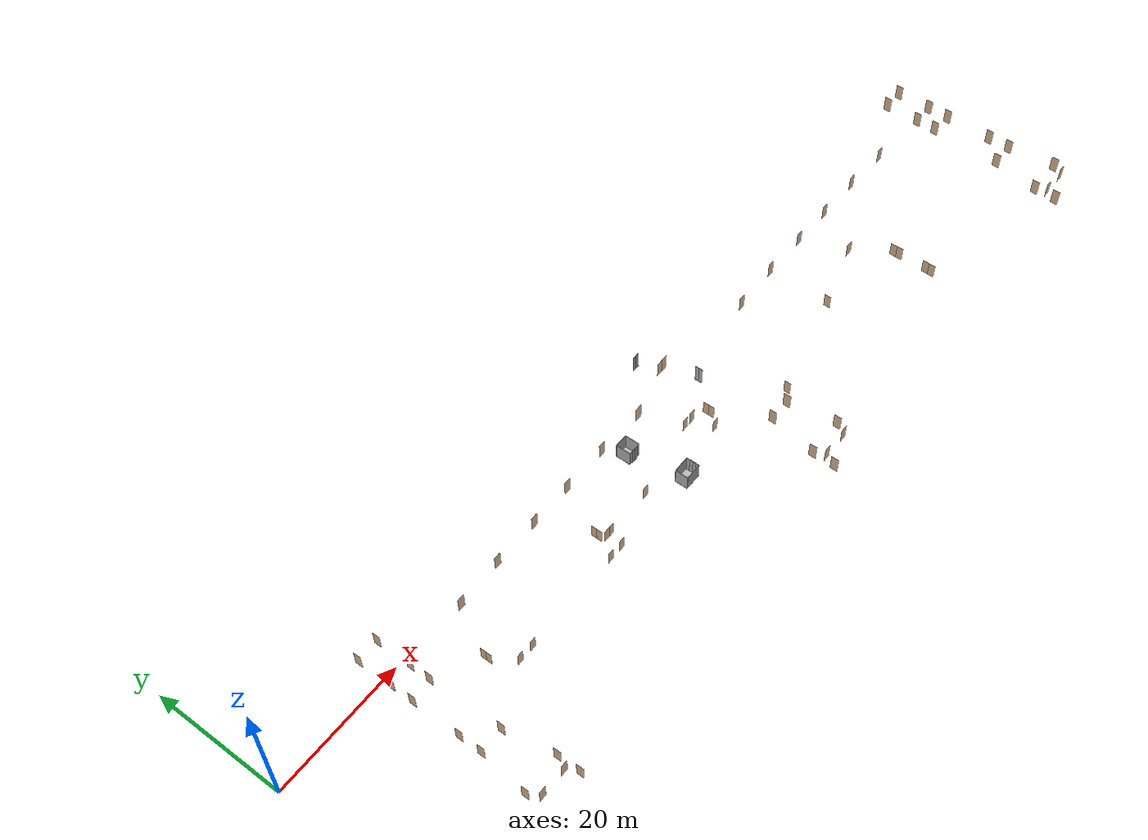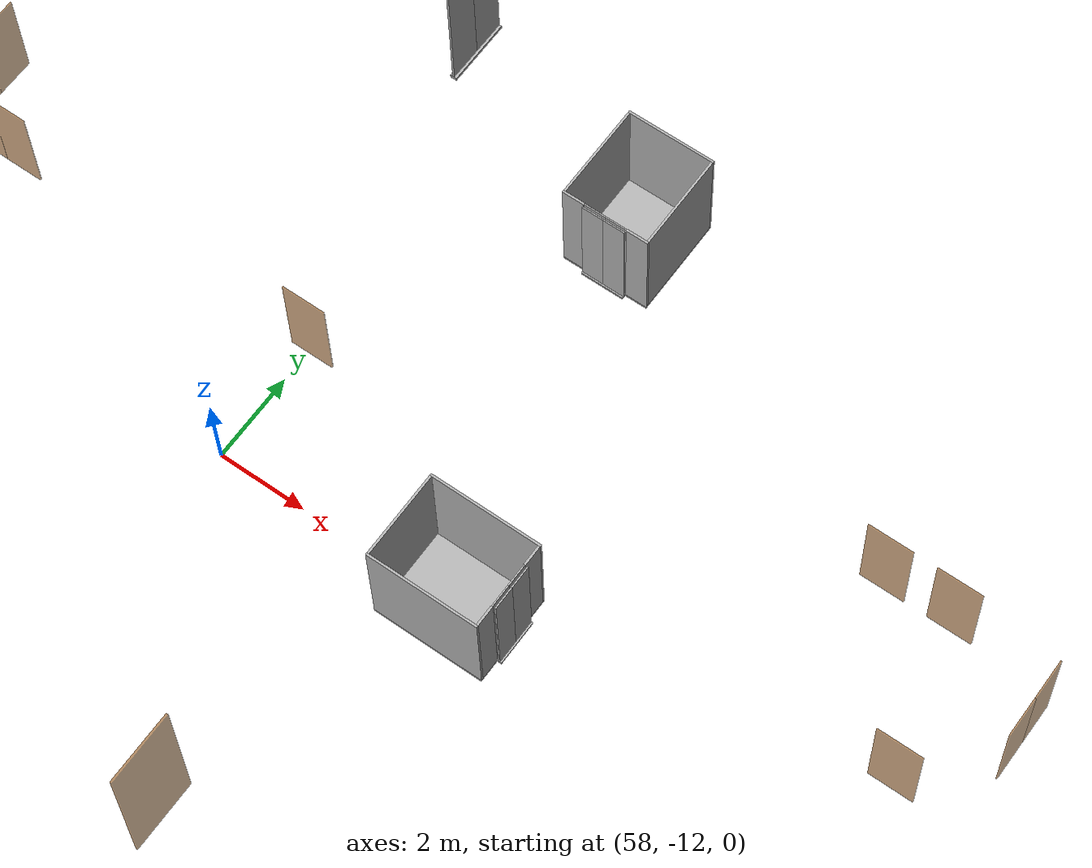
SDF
<sdf version="1.7">
 <world name="sim_world">
  <physics name="10ms" type="ode">
   <max_step_size>0.01</max_step_size>
   <real_time_factor>1.0</real_time_factor>
  </physics>
  <plugin filename="libignition-gazebo-physics-system.so" name="ignition::gazebo::systems::Physics"/>
  <plugin filename="libignition-gazebo-user-commands-system.so" name="ignition::gazebo::systems::UserCommands"/>
  <plugin filename="libignition-gazebo-scene-broadcaster-system.so" name="ignition::gazebo::systems::SceneBroadcaster"/>
  <scene><ambient>1 1 1</ambient><background>0.8 0.8 0.8</background><grid>false</grid></scene>
  <light type="directional" name="sun">
   <pose>0 0 10 0 0 0</pose>
   <diffuse>1 1 1 1</diffuse>
   <specular>0.2 0.2 0.2 1</specular>
   <attenuation>
    <range>1000</range>
    <constant>0.09</constant>
    <linear>0.001</linear>
    <quadratic>0.001</quadratic>
   </attenuation>
   <direction>-0.5 0.1 -0.9</direction>
  </light>
  <model name="l1_door17">
   <pose>27.450000000000003 -8.125 0.0 0 0 -1.5707963267948966</pose>
   <link name="right">
    <pose>-0.4375 0 1.11 0 0 0</pose>
    <visual name="right_visual">
     <geometry><box><size>0.865 0.03 2.2</size></box></geometry>
     <material>
      <ambient>0.5 0.25 0 0.6</ambient>
      <diffuse>0.5 0.25 0 0.6</diffuse>
      <pbr><metal><metalness>0.0</metalness></metal></pbr>
     </material>
    </visual>
    <collision name="right_collision">
     <geometry><box><size>0.865 0.03 2.2</size></box></geometry>
     <surface><contact><collide_bitmask>0x02</collide_bitmask></contact></surface>
    </collision>
    <inertial>
     <mass>50.0</mass>
     <inertia><ixx>20.17041666666667</ixx><iyy>23.284270833333338</iyy><izz>3.121354166666667</izz></inertia>
    </inertial>
   </link>
   <joint name="right_joint" type="revolute">
    <parent>world</parent>
    <child>right</child>
    <axis><xyz>0 0 1</xyz><limit><lower>0</lower><upper>1.57</upper></limit></axis>
    <pose>-0.4375 0 0 0 0 0</pose>
   </joint>
   <link name="left">
    <pose>0.4375 0 1.11 0 0 0</pose>
    <visual name="left_visual">
     <geometry><box><size>0.865 0.03 2.2</size></box></geometry>
     <material>
      <ambient>0.5 0.25 0 0.6</ambient>
      <diffuse>0.5 0.25 0 0.6</diffuse>
      <pbr><metal><metalness>0.0</metalness></metal></pbr>
     </material>
    </visual>
    <collision name="left_collision">
     <geometry><box><size>0.865 0.03 2.2</size></box></geometry>
     <surface><contact><collide_bitmask>0x02</collide_bitmask></contact></surface>
    </collision>
    <inertial>
     <mass>50.0</mass>
     <inertia><ixx>20.17041666666667</ixx><iyy>23.284270833333338</iyy><izz>3.121354166666667</izz></inertia>
    </inertial>
   </link>
   <joint name="left_joint" type="revolute">
    <parent>world</parent>
    <child>left</child>
    <axis><xyz>0 0 1</xyz><limit><lower>-1.57</lower><upper>0</upper></limit></axis>
    <pose>0.4375 0 0 0 0 0</pose>
   </joint>
   <plugin name="door" filename="libdoor.so">
    <v_max_door>0.5</v_max_door>
    <a_max_door>0.3</a_max_door>
    <a_nom_door>0.15</a_nom_door>
    <dx_min_door>0.01</dx_min_door>
    <f_max_door>500.0</f_max_door>
    <door name="l1_door17" type="DoubleSwingDoor" left_joint_name="left_joint" right_joint_name="right_joint"/>
   </plugin>
  </model>
  <model name="l1_door16">
   <pose>49.225 -8.125 0.0 0 0 1.5707963267948966</pose>
   <link name="right">
    <pose>-0.4375 0 1.11 0 0 0</pose>
    <visual name="right_visual">
     <geometry><box><size>0.865 0.03 2.2</size></box></geometry>
     <material>
      <ambient>0.5 0.25 0 0.6</ambient>
      <diffuse>0.5 0.25 0 0.6</diffuse>
      <pbr><metal><metalness>0.0</metalness></metal></pbr>
     </material>
    </visual>
    <collision name="right_collision">
     <geometry><box><size>0.865 0.03 2.2</size></box></geometry>
     <surface><contact><collide_bitmask>0x02</collide_bitmask></contact></surface>
    </collision>
    <inertial>
     <mass>50.0</mass>
     <inertia><ixx>20.17041666666667</ixx><iyy>23.284270833333338</iyy><izz>3.121354166666667</izz></inertia>
    </inertial>
   </link>
   <joint name="right_joint" type="revolute">
    <parent>world</parent>
    <child>right</child>
    <axis><xyz>0 0 1</xyz><limit><lower>0</lower><upper>1.57</upper></limit></axis>
    <pose>-0.4375 0 0 0 0 0</pose>
   </joint>
   <link name="left">
    <pose>0.4375 0 1.11 0 0 0</pose>
    <visual name="left_visual">
     <geometry><box><size>0.865 0.03 2.2</size></box></geometry>
     <material>
      <ambient>0.5 0.25 0 0.6</ambient>
      <diffuse>0.5 0.25 0 0.6</diffuse>
      <pbr><metal><metalness>0.0</metalness></metal></pbr>
     </material>
    </visual>
    <collision name="left_collision">
     <geometry><box><size>0.865 0.03 2.2</size></box></geometry>
     <surface><contact><collide_bitmask>0x02</collide_bitmask></contact></surface>
    </collision>
    <inertial>
     <mass>50.0</mass>
     <inertia><ixx>20.17041666666667</ixx><iyy>23.284270833333338</iyy><izz>3.121354166666667</izz></inertia>
    </inertial>
   </link>
   <joint name="left_joint" type="revolute">
    <parent>world</parent>
    <child>left</child>
    <axis><xyz>0 0 1</xyz><limit><lower>-1.57</lower><upper>0</upper></limit></axis>
    <pose>0.4375 0 0 0 0 0</pose>
   </joint>
   <plugin name="door" filename="libdoor.so">
    <v_max_door>0.5</v_max_door>
    <a_max_door>0.3</a_max_door>
    <a_nom_door>0.15</a_nom_door>
    <dx_min_door>0.01</dx_min_door>
    <f_max_door>500.0</f_max_door>
    <door name="l1_door16" type="DoubleSwingDoor" left_joint_name="left_joint" right_joint_name="right_joint"/>
   </plugin>
  </model>
  <model name="l1_door15">
   <pose>50.35 -9.25 0.0 0 0 3.141592653589793</pose>
   <link name="right">
    <pose>-0.4375 0 1.11 0 0 0</pose>
    <visual name="right_visual">
     <geometry><box><size>0.865 0.03 2.2</size></box></geometry>
     <material>
      <ambient>0.5 0.25 0 0.6</ambient>
      <diffuse>0.5 0.25 0 0.6</diffuse>
      <pbr><metal><metalness>0.0</metalness></metal></pbr>
     </material>
    </visual>
    <collision name="right_collision">
     <geometry><box><size>0.865 0.03 2.2</size></box></geometry>
     <surface><contact><collide_bitmask>0x02</collide_bitmask></contact></surface>
    </collision>
    <inertial>
     <mass>50.0</mass>
     <inertia><ixx>20.17041666666667</ixx><iyy>23.284270833333338</iyy><izz>3.121354166666667</izz></inertia>
    </inertial>
   </link>
   <joint name="right_joint" type="revolute">
    <parent>world</parent>
    <child>right</child>
    <axis><xyz>0 0 1</xyz><limit><lower>0</lower><upper>1.57</upper></limit></axis>
    <pose>-0.4375 0 0 0 0 0</pose>
   </joint>
   <link name="left">
    <pose>0.4375 0 1.11 0 0 0</pose>
    <visual name="left_visual">
     <geometry><box><size>0.865 0.03 2.2</size></box></geometry>
     <material>
      <ambient>0.5 0.25 0 0.6</ambient>
      <diffuse>0.5 0.25 0 0.6</diffuse>
      <pbr><metal><metalness>0.0</metalness></metal></pbr>
     </material>
    </visual>
    <collision name="left_collision">
     <geometry><box><size>0.865 0.03 2.2</size></box></geometry>
     <surface><contact><collide_bitmask>0x02</collide_bitmask></contact></surface>
    </collision>
    <inertial>
     <mass>50.0</mass>
     <inertia><ixx>20.17041666666667</ixx><iyy>23.284270833333338</iyy><izz>3.121354166666667</izz></inertia>
    </inertial>
   </link>
   <joint name="left_joint" type="revolute">
    <parent>world</parent>
    <child>left</child>
    <axis><xyz>0 0 1</xyz><limit><lower>-1.57</lower><upper>0</upper></limit></axis>
    <pose>0.4375 0 0 0 0 0</pose>
   </joint>
   <plugin name="door" filename="libdoor.so">
    <v_max_door>0.5</v_max_door>
    <a_max_door>0.3</a_max_door>
    <a_nom_door>0.15</a_nom_door>
    <dx_min_door>0.01</dx_min_door>
    <f_max_door>500.0</f_max_door>
    <door name="l1_door15" type="DoubleSwingDoor" left_joint_name="left_joint" right_joint_name="right_joint"/>
   </plugin>
  </model>
  <model name="dining_4">
   <pose>29.75 -11.600000000000001 0.0 0 0 3.141592653589793</pose>
   <plugin name="door" filename="libdoor.so">
    <v_max_door>0.5</v_max_door>
    <a_max_door>0.3</a_max_door>
    <a_nom_door>0.15</a_nom_door>
    <dx_min_door>0.01</dx_min_door>
    <f_max_door>500.0</f_max_door>
    <door name="dining_4" type="SwingDoor" left_joint_name="left_joint" right_joint_name="empty_joint"/>
   </plugin>
   <link name="left">
    <pose>0 0 1.11 0 0 0</pose>
    <visual name="left_visual">
     <geometry><box><size>0.99 0.03 2.2</size></box></geometry>
     <material>
      <ambient>0.5 0.25 0 0.6</ambient>
      <diffuse>0.5 0.25 0 0.6</diffuse>
      <pbr><metal><metalness>0.0</metalness></metal></pbr>
     </material>
    </visual>
    <collision name="left_collision">
     <geometry><box><size>0.99 0.03 2.2</size></box></geometry>
     <surface><contact><collide_bitmask>0x02</collide_bitmask></contact></surface>
    </collision>
    <inertial>
     <mass>50.0</mass>
     <inertia><ixx>20.17041666666667</ixx><iyy>24.250416666666673</iyy><izz>4.0875</izz></inertia>
    </inertial>
   </link>
   <joint name="left_joint" type="revolute">
    <parent>world</parent>
    <child>left</child>
    <axis><xyz>0 0 1</xyz><limit><lower>-1.57</lower><upper>0</upper></limit></axis>
    <pose>0.5 0 0 0 0 0</pose>
   </joint>
  </model>
  <model name="dining_3">
   <pose>32.1 -11.600000000000001 0.0 0 0 0.0</pose>
   <plugin name="door" filename="libdoor.so">
    <v_max_door>0.5</v_max_door>
    <a_max_door>0.3</a_max_door>
    <a_nom_door>0.15</a_nom_door>
    <dx_min_door>0.01</dx_min_door>
    <f_max_door>500.0</f_max_door>
    <door name="dining_3" type="SwingDoor" left_joint_name="empty_joint" right_joint_name="right_joint"/>
   </plugin>
   <link name="right">
    <pose>0 0 1.11 0 0 0</pose>
    <visual name="right_visual">
     <geometry><box><size>0.99 0.03 2.2</size></box></geometry>
     <material>
      <ambient>0.5 0.25 0 0.6</ambient>
      <diffuse>0.5 0.25 0 0.6</diffuse>
      <pbr><metal><metalness>0.0</metalness></metal></pbr>
     </material>
    </visual>
    <collision name="right_collision">
     <geometry><box><size>0.99 0.03 2.2</size></box></geometry>
     <surface><contact><collide_bitmask>0x02</collide_bitmask></contact></surface>
    </collision>
    <inertial>
     <mass>50.0</mass>
     <inertia><ixx>20.17041666666667</ixx><iyy>24.250416666666673</iyy><izz>4.0875</izz></inertia>
    </inertial>
   </link>
   <joint name="right_joint" type="revolute">
    <parent>world</parent>
    <child>right</child>
    <axis><xyz>0 0 1</xyz><limit><lower>0</lower><upper>1.57</upper></limit></axis>
    <pose>0.5 0 0 0 0 0</pose>
   </joint>
  </model>
  <model name="dining_2">
   <pose>47.650000000000006 -11.600000000000001 0.0 0 0 3.141592653589793</pose>
   <plugin name="door" filename="libdoor.so">
    <v_max_door>0.5</v_max_door>
    <a_max_door>0.3</a_max_door>
    <a_nom_door>0.15</a_nom_door>
    <dx_min_door>0.01</dx_min_door>
    <f_max_door>500.0</f_max_door>
    <door name="dining_2" type="SwingDoor" left_joint_name="left_joint" right_joint_name="empty_joint"/>
   </plugin>
   <link name="left">
    <pose>0 0 1.11 0 0 0</pose>
    <visual name="left_visual">
     <geometry><box><size>0.99 0.03 2.2</size></box></geometry>
     <material>
      <ambient>0.5 0.25 0 0.6</ambient>
      <diffuse>0.5 0.25 0 0.6</diffuse>
      <pbr><metal><metalness>0.0</metalness></metal></pbr>
     </material>
    </visual>
    <collision name="left_collision">
     <geometry><box><size>0.99 0.03 2.2</size></box></geometry>
     <surface><contact><collide_bitmask>0x02</collide_bitmask></contact></surface>
    </collision>
    <inertial>
     <mass>50.0</mass>
     <inertia><ixx>20.17041666666667</ixx><iyy>24.250416666666673</iyy><izz>4.0875</izz></inertia>
    </inertial>
   </link>
   <joint name="left_joint" type="revolute">
    <parent>world</parent>
    <child>left</child>
    <axis><xyz>0 0 1</xyz><limit><lower>-1.57</lower><upper>0</upper></limit></axis>
    <pose>0.5 0 0 0 0 0</pose>
   </joint>
  </model>
  <model name="dining_1">
   <pose>50.0 -11.600000000000001 0.0 0 0 0.0</pose>
   <plugin name="door" filename="libdoor.so">
    <v_max_door>0.5</v_max_door>
    <a_max_door>0.3</a_max_door>
    <a_nom_door>0.15</a_nom_door>
    <dx_min_door>0.01</dx_min_door>
    <f_max_door>500.0</f_max_door>
    <door name="dining_1" type="SwingDoor" left_joint_name="empty_joint" right_joint_name="right_joint"/>
   </plugin>
   <link name="right">
    <pose>0 0 1.11 0 0 0</pose>
    <visual name="right_visual">
     <geometry><box><size>0.99 0.03 2.2</size></box></geometry>
     <material>
      <ambient>0.5 0.25 0 0.6</ambient>
      <diffuse>0.5 0.25 0 0.6</diffuse>
      <pbr><metal><metalness>0.0</metalness></metal></pbr>
     </material>
    </visual>
    <collision name="right_collision">
     <geometry><box><size>0.99 0.03 2.2</size></box></geometry>
     <surface><contact><collide_bitmask>0x02</collide_bitmask></contact></surface>
    </collision>
    <inertial>
     <mass>50.0</mass>
     <inertia><ixx>20.17041666666667</ixx><iyy>24.250416666666673</iyy><izz>4.0875</izz></inertia>
    </inertial>
   </link>
   <joint name="right_joint" type="revolute">
    <parent>world</parent>
    <child>right</child>
    <axis><xyz>0 0 1</xyz><limit><lower>0</lower><upper>1.57</upper></limit></axis>
    <pose>0.5 0 0 0 0 0</pose>
   </joint>
  </model>
  <model name="l1_door12">
   <pose>58.1 -9.25 0.0 0 0 3.141592653589793</pose>
   <plugin name="door" filename="libdoor.so">
    <v_max_door>0.5</v_max_door>
    <a_max_door>0.3</a_max_door>
    <a_nom_door>0.15</a_nom_door>
    <dx_min_door>0.01</dx_min_door>
    <f_max_door>500.0</f_max_door>
    <door name="l1_door12" type="SwingDoor" left_joint_name="left_joint" right_joint_name="empty_joint"/>
   </plugin>
   <link name="left">
    <pose>0 0 1.11 0 0 0</pose>
    <visual name="left_visual">
     <geometry><box><size>0.99 0.03 2.2</size></box></geometry>
     <material>
      <ambient>0.5 0.25 0 0.6</ambient>
      <diffuse>0.5 0.25 0 0.6</diffuse>
      <pbr><metal><metalness>0.0</metalness></metal></pbr>
     </material>
    </visual>
    <collision name="left_collision">
     <geometry><box><size>0.99 0.03 2.2</size></box></geometry>
     <surface><contact><collide_bitmask>0x02</collide_bitmask></contact></surface>
    </collision>
    <inertial>
     <mass>50.0</mass>
     <inertia><ixx>20.17041666666667</ixx><iyy>24.250416666666673</iyy><izz>4.0875</izz></inertia>
    </inertial>
   </link>
   <joint name="left_joint" type="revolute">
    <parent>world</parent>
    <child>left</child>
    <axis><xyz>0 0 1</xyz><limit><lower>-1.57</lower><upper>0</upper></limit></axis>
    <pose>0.5 0 0 0 0 0</pose>
   </joint>
  </model>
  <model name="l1_door10">
   <pose>69.9 -7.0 0.0 0 0 0.0</pose>
   <plugin name="door" filename="libdoor.so">
    <v_max_door>0.5</v_max_door>
    <a_max_door>0.3</a_max_door>
    <a_nom_door>0.15</a_nom_door>
    <dx_min_door>0.01</dx_min_door>
    <f_max_door>500.0</f_max_door>
    <door name="l1_door10" type="SwingDoor" left_joint_name="left_joint" right_joint_name="empty_joint"/>
   </plugin>
   <link name="left">
    <pose>0 0 1.11 0 0 0</pose>
    <visual name="left_visual">
     <geometry><box><size>0.99 0.03 2.2</size></box></geometry>
     <material>
      <ambient>0.5 0.25 0 0.6</ambient>
      <diffuse>0.5 0.25 0 0.6</diffuse>
      <pbr><metal><metalness>0.0</metalness></metal></pbr>
     </material>
    </visual>
    <collision name="left_collision">
     <geometry><box><size>0.99 0.03 2.2</size></box></geometry>
     <surface><contact><collide_bitmask>0x02</collide_bitmask></contact></surface>
    </collision>
    <inertial>
     <mass>50.0</mass>
     <inertia><ixx>20.17041666666667</ixx><iyy>24.250416666666673</iyy><izz>4.0875</izz></inertia>
    </inertial>
   </link>
   <joint name="left_joint" type="revolute">
    <parent>world</parent>
    <child>left</child>
    <axis><xyz>0 0 1</xyz><limit><lower>-1.57</lower><upper>0</upper></limit></axis>
    <pose>0.5 0 0 0 0 0</pose>
   </joint>
  </model>
  <model name="l1_door8">
   <pose>71.4 -7.0 0.0 0 0 3.141592653589793</pose>
   <plugin name="door" filename="libdoor.so">
    <v_max_door>0.5</v_max_door>
    <a_max_door>0.3</a_max_door>
    <a_nom_door>0.15</a_nom_door>
    <dx_min_door>0.01</dx_min_door>
    <f_max_door>500.0</f_max_door>
    <door name="l1_door8" type="SwingDoor" left_joint_name="empty_joint" right_joint_name="right_joint"/>
   </plugin>
   <link name="right">
    <pose>0 0 1.11 0 0 0</pose>
    <visual name="right_visual">
     <geometry><box><size>0.99 0.03 2.2</size></box></geometry>
     <material>
      <ambient>0.5 0.25 0 0.6</ambient>
      <diffuse>0.5 0.25 0 0.6</diffuse>
      <pbr><metal><metalness>0.0</metalness></metal></pbr>
     </material>
    </visual>
    <collision name="right_collision">
     <geometry><box><size>0.99 0.03 2.2</size></box></geometry>
     <surface><contact><collide_bitmask>0x02</collide_bitmask></contact></surface>
    </collision>
    <inertial>
     <mass>50.0</mass>
     <inertia><ixx>20.17041666666667</ixx><iyy>24.250416666666673</iyy><izz>4.0875</izz></inertia>
    </inertial>
   </link>
   <joint name="right_joint" type="revolute">
    <parent>world</parent>
    <child>right</child>
    <axis><xyz>0 0 1</xyz><limit><lower>0</lower><upper>1.57</upper></limit></axis>
    <pose>0.5 0 0 0 0 0</pose>
   </joint>
  </model>
  <model name="l1_door6">
   <pose>72.2 -10.25 0.0 0 0 3.141592653589793</pose>
   <plugin name="door" filename="libdoor.so">
    <v_max_door>0.5</v_max_door>
    <a_max_door>0.3</a_max_door>
    <a_nom_door>0.15</a_nom_door>
    <dx_min_door>0.01</dx_min_door>
    <f_max_door>500.0</f_max_door>
    <door name="l1_door6" type="SwingDoor" left_joint_name="empty_joint" right_joint_name="right_joint"/>
   </plugin>
   <link name="right">
    <pose>0 0 1.11 0 0 0</pose>
    <visual name="right_visual">
     <geometry><box><size>0.99 0.03 2.2</size></box></geometry>
     <material>
      <ambient>0.5 0.25 0 0.6</ambient>
      <diffuse>0.5 0.25 0 0.6</diffuse>
      <pbr><metal><metalness>0.0</metalness></metal></pbr>
     </material>
    </visual>
    <collision name="right_collision">
     <geometry><box><size>0.99 0.03 2.2</size></box></geometry>
     <surface><contact><collide_bitmask>0x02</collide_bitmask></contact></surface>
    </collision>
    <inertial>
     <mass>50.0</mass>
     <inertia><ixx>20.17041666666667</ixx><iyy>24.250416666666673</iyy><izz>4.0875</izz></inertia>
    </inertial>
   </link>
   <joint name="right_joint" type="revolute">
    <parent>world</parent>
    <child>right</child>
    <axis><xyz>0 0 1</xyz><limit><lower>0</lower><upper>1.57</upper></limit></axis>
    <pose>0.5 0 0 0 0 0</pose>
   </joint>
  </model>
  <model name="l1_door7">
   <pose>73.7 -8.125 0.0 0 0 -1.5707963267948966</pose>
   <link name="right">
    <pose>-0.4375 0 1.11 0 0 0</pose>
    <visual name="right_visual">
     <geometry><box><size>0.865 0.03 2.2</size></box></geometry>
     <material>
      <ambient>0.5 0.25 0 0.6</ambient>
      <diffuse>0.5 0.25 0 0.6</diffuse>
      <pbr><metal><metalness>0.0</metalness></metal></pbr>
     </material>
    </visual>
    <collision name="right_collision">
     <geometry><box><size>0.865 0.03 2.2</size></box></geometry>
     <surface><contact><collide_bitmask>0x02</collide_bitmask></contact></surface>
    </collision>
    <inertial>
     <mass>50.0</mass>
     <inertia><ixx>20.17041666666667</ixx><iyy>23.284270833333338</iyy><izz>3.121354166666667</izz></inertia>
    </inertial>
   </link>
   <joint name="right_joint" type="revolute">
    <parent>world</parent>
    <child>right</child>
    <axis><xyz>0 0 1</xyz><limit><lower>0</lower><upper>1.57</upper></limit></axis>
    <pose>-0.4375 0 0 0 0 0</pose>
   </joint>
   <link name="left">
    <pose>0.4375 0 1.11 0 0 0</pose>
    <visual name="left_visual">
     <geometry><box><size>0.865 0.03 2.2</size></box></geometry>
     <material>
      <ambient>0.5 0.25 0 0.6</ambient>
      <diffuse>0.5 0.25 0 0.6</diffuse>
      <pbr><metal><metalness>0.0</metalness></metal></pbr>
     </material>
    </visual>
    <collision name="left_collision">
     <geometry><box><size>0.865 0.03 2.2</size></box></geometry>
     <surface><contact><collide_bitmask>0x02</collide_bitmask></contact></surface>
    </collision>
    <inertial>
     <mass>50.0</mass>
     <inertia><ixx>20.17041666666667</ixx><iyy>23.284270833333338</iyy><izz>3.121354166666667</izz></inertia>
    </inertial>
   </link>
   <joint name="left_joint" type="revolute">
    <parent>world</parent>
    <child>left</child>
    <axis><xyz>0 0 1</xyz><limit><lower>-1.57</lower><upper>0</upper></limit></axis>
    <pose>0.4375 0 0 0 0 0</pose>
   </joint>
   <plugin name="door" filename="libdoor.so">
    <v_max_door>0.5</v_max_door>
    <a_max_door>0.3</a_max_door>
    <a_nom_door>0.15</a_nom_door>
    <dx_min_door>0.01</dx_min_door>
    <f_max_door>500.0</f_max_door>
    <door name="l1_door7" type="DoubleSwingDoor" left_joint_name="left_joint" right_joint_name="right_joint"/>
   </plugin>
  </model>
  <model name="l1_door3">
   <pose>109.47500000000001 -7.5 0.0 0 0 0.0</pose>
   <plugin name="door" filename="libdoor.so">
    <v_max_door>0.5</v_max_door>
    <a_max_door>0.3</a_max_door>
    <a_nom_door>0.15</a_nom_door>
    <dx_min_door>0.01</dx_min_door>
    <f_max_door>500.0</f_max_door>
    <door name="l1_door3" type="SwingDoor" left_joint_name="left_joint" right_joint_name="empty_joint"/>
   </plugin>
   <link name="left">
    <pose>0 0 1.11 0 0 0</pose>
    <visual name="left_visual">
     <geometry><box><size>1.24 0.03 2.2</size></box></geometry>
     <material>
      <ambient>0.5 0.25 0 0.6</ambient>
      <diffuse>0.5 0.25 0 0.6</diffuse>
      <pbr><metal><metalness>0.0</metalness></metal></pbr>
     </material>
    </visual>
    <collision name="left_collision">
     <geometry><box><size>1.24 0.03 2.2</size></box></geometry>
     <surface><contact><collide_bitmask>0x02</collide_bitmask></contact></surface>
    </collision>
    <inertial>
     <mass>50.0</mass>
     <inertia><ixx>20.17041666666667</ixx><iyy>26.57333333333334</iyy><izz>6.410416666666667</izz></inertia>
    </inertial>
   </link>
   <joint name="left_joint" type="revolute">
    <parent>world</parent>
    <child>left</child>
    <axis><xyz>0 0 1</xyz><limit><lower>-1.57</lower><upper>0</upper></limit></axis>
    <pose>0.625 0 0 0 0 0</pose>
   </joint>
  </model>
  <model name="entrance_2">
   <pose>113.15 -13.25 0.0 0 0 1.5707963267948966</pose>
   <link name="left">
    <pose>-0.5 0 1.11 0 0 0</pose>
    <visual name="left_visual">
     <geometry><box><size>0.99 0.03 2.2</size></box></geometry>
     <material>
      <ambient>0.5 0.25 0 0.6</ambient>
      <diffuse>0.5 0.25 0 0.6</diffuse>
      <pbr><metal><metalness>0.0</metalness></metal></pbr>
     </material>
    </visual>
    <collision name="left_collision">
     <geometry><box><size>0.99 0.03 2.2</size></box></geometry>
     <surface><contact><collide_bitmask>0x02</collide_bitmask></contact></surface>
    </collision>
    <inertial>
     <mass>50.0</mass>
     <inertia><ixx>20.17041666666667</ixx><iyy>24.250416666666673</iyy><izz>4.0875</izz></inertia>
    </inertial>
   </link>
   <joint name="left_joint" type="prismatic">
    <parent>world</parent>
    <child>left</child>
    <axis><xyz>1 0 0</xyz><limit><lower>-1.0</lower><upper>0.0</upper><effort>500.0</effort></limit></axis>
   </joint>
   <link name="right">
    <pose>0.5 0 1.11 0 0 0</pose>
    <visual name="right_visual">
     <geometry><box><size>0.99 0.03 2.2</size></box></geometry>
     <material>
      <ambient>0.5 0.25 0 0.6</ambient>
      <diffuse>0.5 0.25 0 0.6</diffuse>
      <pbr><metal><metalness>0.0</metalness></metal></pbr>
     </material>
    </visual>
    <collision name="right_collision">
     <geometry><box><size>0.99 0.03 2.2</size></box></geometry>
     <surface><contact><collide_bitmask>0x02</collide_bitmask></contact></surface>
    </collision>
    <inertial>
     <mass>50.0</mass>
     <inertia><ixx>20.17041666666667</ixx><iyy>24.250416666666673</iyy><izz>4.0875</izz></inertia>
    </inertial>
   </link>
   <joint name="right_joint" type="prismatic">
    <parent>world</parent>
    <child>right</child>
    <axis><xyz>1 0 0</xyz><limit><lower>0.0</lower><upper>1.0</upper><effort>500.0</effort></limit></axis>
   </joint>
   <plugin name="door" filename="libdoor.so">
    <v_max_door>0.2</v_max_door>
    <a_max_door>0.2</a_max_door>
    <a_nom_door>0.08</a_nom_door>
    <dx_min_door>0.001</dx_min_door>
    <f_max_door>100.0</f_max_door>
    <door name="entrance_2" type="DoubleSlidingDoor" left_joint_name="left_joint" right_joint_name="right_joint"/>
   </plugin>
  </model>
  <model name="entrance_1">
   <pose>113.15 -18.6 0.0 0 0 1.5707963267948966</pose>
   <link name="left">
    <pose>-0.5 0 1.11 0 0 0</pose>
    <visual name="left_visual">
     <geometry><box><size>0.99 0.03 2.2</size></box></geometry>
     <material>
      <ambient>0.5 0.25 0 0.6</ambient>
      <diffuse>0.5 0.25 0 0.6</diffuse>
      <pbr><metal><metalness>0.0</metalness></metal></pbr>
     </material>
    </visual>
    <collision name="left_collision">
     <geometry><box><size>0.99 0.03 2.2</size></box></geometry>
     <surface><contact><collide_bitmask>0x02</collide_bitmask></contact></surface>
    </collision>
    <inertial>
     <mass>50.0</mass>
     <inertia><ixx>20.17041666666667</ixx><iyy>24.250416666666673</iyy><izz>4.0875</izz></inertia>
    </inertial>
   </link>
   <joint name="left_joint" type="prismatic">
    <parent>world</parent>
    <child>left</child>
    <axis><xyz>1 0 0</xyz><limit><lower>-1.0</lower><upper>0.0</upper><effort>500.0</effort></limit></axis>
   </joint>
   <link name="right">
    <pose>0.5 0 1.11 0 0 0</pose>
    <visual name="right_visual">
     <geometry><box><size>0.99 0.03 2.2</size></box></geometry>
     <material>
      <ambient>0.5 0.25 0 0.6</ambient>
      <diffuse>0.5 0.25 0 0.6</diffuse>
      <pbr><metal><metalness>0.0</metalness></metal></pbr>
     </material>
    </visual>
    <collision name="right_collision">
     <geometry><box><size>0.99 0.03 2.2</size></box></geometry>
     <surface><contact><collide_bitmask>0x02</collide_bitmask></contact></surface>
    </collision>
    <inertial>
     <mass>50.0</mass>
     <inertia><ixx>20.17041666666667</ixx><iyy>24.250416666666673</iyy><izz>4.0875</izz></inertia>
    </inertial>
   </link>
   <joint name="right_joint" type="prismatic">
    <parent>world</parent>
    <child>right</child>
    <axis><xyz>1 0 0</xyz><limit><lower>0.0</lower><upper>1.0</upper><effort>500.0</effort></limit></axis>
   </joint>
   <plugin name="door" filename="libdoor.so">
    <v_max_door>0.2</v_max_door>
    <a_max_door>0.2</a_max_door>
    <a_nom_door>0.08</a_nom_door>
    <dx_min_door>0.001</dx_min_door>
    <f_max_door>100.0</f_max_door>
    <door name="entrance_1" type="DoubleSlidingDoor" left_joint_name="left_joint" right_joint_name="right_joint"/>
   </plugin>
  </model>
  <model name="l1_door5">
   <pose>99.30000000000001 -10.4 0.0 0 0 1.5707963267948966</pose>
   <plugin name="door" filename="libdoor.so">
    <v_max_door>0.5</v_max_door>
    <a_max_door>0.3</a_max_door>
    <a_nom_door>0.15</a_nom_door>
    <dx_min_door>0.01</dx_min_door>
    <f_max_door>500.0</f_max_door>
    <door name="l1_door5" type="SwingDoor" left_joint_name="left_joint" right_joint_name="empty_joint"/>
   </plugin>
   <link name="left">
    <pose>0 0 1.11 0 0 0</pose>
    <visual name="left_visual">
     <geometry><box><size>0.99 0.03 2.2</size></box></geometry>
     <material>
      <ambient>0.5 0.25 0 0.6</ambient>
      <diffuse>0.5 0.25 0 0.6</diffuse>
      <pbr><metal><metalness>0.0</metalness></metal></pbr>
     </material>
    </visual>
    <collision name="left_collision">
     <geometry><box><size>0.99 0.03 2.2</size></box></geometry>
     <surface><contact><collide_bitmask>0x02</collide_bitmask></contact></surface>
    </collision>
    <inertial>
     <mass>50.0</mass>
     <inertia><ixx>20.17041666666667</ixx><iyy>24.250416666666673</iyy><izz>4.0875</izz></inertia>
    </inertial>
   </link>
   <joint name="left_joint" type="revolute">
    <parent>world</parent>
    <child>left</child>
    <axis><xyz>0 0 1</xyz><limit><lower>-1.57</lower><upper>0</upper></limit></axis>
    <pose>0.5 0 0 0 0 0</pose>
   </joint>
  </model>
  <model name="restroom_cleaning_door">
   <pose>83.25 -14.4 0.0 0 0 -1.5707963267948966</pose>
   <plugin name="door" filename="libdoor.so">
    <v_max_door>0.5</v_max_door>
    <a_max_door>0.3</a_max_door>
    <a_nom_door>0.15</a_nom_door>
    <dx_min_door>0.01</dx_min_door>
    <f_max_door>500.0</f_max_door>
    <door name="restroom_cleaning_door" type="SwingDoor" left_joint_name="left_joint" right_joint_name="empty_joint"/>
   </plugin>
   <link name="left">
    <pose>0 0 1.11 0 0 0</pose>
    <visual name="left_visual">
     <geometry><box><size>0.99 0.03 2.2</size></box></geometry>
     <material>
      <ambient>0.5 0.25 0 0.6</ambient>
      <diffuse>0.5 0.25 0 0.6</diffuse>
      <pbr><metal><metalness>0.0</metalness></metal></pbr>
     </material>
    </visual>
    <collision name="left_collision">
     <geometry><box><size>0.99 0.03 2.2</size></box></geometry>
     <surface><contact><collide_bitmask>0x02</collide_bitmask></contact></surface>
    </collision>
    <inertial>
     <mass>50.0</mass>
     <inertia><ixx>20.17041666666667</ixx><iyy>24.250416666666673</iyy><izz>4.0875</izz></inertia>
    </inertial>
   </link>
   <joint name="left_joint" type="revolute">
    <parent>world</parent>
    <child>left</child>
    <axis><xyz>0 0 1</xyz><limit><lower>-1.57</lower><upper>0</upper></limit></axis>
    <pose>0.5 0 0 0 0 0</pose>
   </joint>
  </model>
  <model name="room1_door">
   <pose>14.7 -5.25 20.0 0 0 -1.5707963267948966</pose>
   <plugin name="door" filename="libdoor.so">
    <v_max_door>0.5</v_max_door>
    <a_max_door>0.3</a_max_door>
    <a_nom_door>0.15</a_nom_door>
    <dx_min_door>0.01</dx_min_door>
    <f_max_door>500.0</f_max_door>
    <door name="room1_door" type="SwingDoor" left_joint_name="left_joint" right_joint_name="empty_joint"/>
   </plugin>
   <link name="left">
    <pose>0 0 1.11 0 0 0</pose>
    <visual name="left_visual">
     <geometry><box><size>0.99 0.03 2.2</size></box></geometry>
     <material>
      <ambient>0.5 0.25 0 0.6</ambient>
      <diffuse>0.5 0.25 0 0.6</diffuse>
      <pbr><metal><metalness>0.0</metalness></metal></pbr>
     </material>
    </visual>
    <collision name="left_collision">
     <geometry><box><size>0.99 0.03 2.2</size></box></geometry>
     <surface><contact><collide_bitmask>0x02</collide_bitmask></contact></surface>
    </collision>
    <inertial>
     <mass>50.0</mass>
     <inertia><ixx>20.17041666666667</ixx><iyy>24.250416666666673</iyy><izz>4.0875</izz></inertia>
    </inertial>
   </link>
   <joint name="left_joint" type="revolute">
    <parent>world</parent>
    <child>left</child>
    <axis><xyz>0 0 1</xyz><limit><lower>-1.57</lower><upper>0</upper></limit></axis>
    <pose>0.5 0 0 0 0 0</pose>
   </joint>
  </model>
  <model name="room2_door">
   <pose>11.7 -5.25 20.0 0 0 -1.5707963267948966</pose>
   <plugin name="door" filename="libdoor.so">
    <v_max_door>0.5</v_max_door>
    <a_max_door>0.3</a_max_door>
    <a_nom_door>0.15</a_nom_door>
    <dx_min_door>0.01</dx_min_door>
    <f_max_door>500.0</f_max_door>
    <door name="room2_door" type="SwingDoor" left_joint_name="empty_joint" right_joint_name="right_joint"/>
   </plugin>
   <link name="right">
    <pose>0 0 1.11 0 0 0</pose>
    <visual name="right_visual">
     <geometry><box><size>0.99 0.03 2.2</size></box></geometry>
     <material>
      <ambient>0.5 0.25 0 0.6</ambient>
      <diffuse>0.5 0.25 0 0.6</diffuse>
      <pbr><metal><metalness>0.0</metalness></metal></pbr>
     </material>
    </visual>
    <collision name="right_collision">
     <geometry><box><size>0.99 0.03 2.2</size></box></geometry>
     <surface><contact><collide_bitmask>0x02</collide_bitmask></contact></surface>
    </collision>
    <inertial>
     <mass>50.0</mass>
     <inertia><ixx>20.17041666666667</ixx><iyy>24.250416666666673</iyy><izz>4.0875</izz></inertia>
    </inertial>
   </link>
   <joint name="right_joint" type="revolute">
    <parent>world</parent>
    <child>right</child>
    <axis><xyz>0 0 1</xyz><limit><lower>0</lower><upper>1.57</upper></limit></axis>
    <pose>0.5 0 0 0 0 0</pose>
   </joint>
  </model>
  <model name="room3_door">
   <pose>11.7 -10.0 20.0 0 0 -1.5707963267948966</pose>
   <plugin name="door" filename="libdoor.so">
    <v_max_door>0.5</v_max_door>
    <a_max_door>0.3</a_max_door>
    <a_nom_door>0.15</a_nom_door>
    <dx_min_door>0.01</dx_min_door>
    <f_max_door>500.0</f_max_door>
    <door name="room3_door" type="SwingDoor" left_joint_name="empty_joint" right_joint_name="right_joint"/>
   </plugin>
   <link name="right">
    <pose>0 0 1.11 0 0 0</pose>
    <visual name="right_visual">
     <geometry><box><size>0.99 0.03 2.2</size></box></geometry>
     <material>
      <ambient>0.5 0.25 0 0.6</ambient>
      <diffuse>0.5 0.25 0 0.6</diffuse>
      <pbr><metal><metalness>0.0</metalness></metal></pbr>
     </material>
    </visual>
    <collision name="right_collision">
     <geometry><box><size>0.99 0.03 2.2</size></box></geometry>
     <surface><contact><collide_bitmask>0x02</collide_bitmask></contact></surface>
    </collision>
    <inertial>
     <mass>50.0</mass>
     <inertia><ixx>20.17041666666667</ixx><iyy>24.250416666666673</iyy><izz>4.0875</izz></inertia>
    </inertial>
   </link>
   <joint name="right_joint" type="revolute">
    <parent>world</parent>
    <child>right</child>
    <axis><xyz>0 0 1</xyz><limit><lower>0</lower><upper>1.57</upper></limit></axis>
    <pose>0.5 0 0 0 0 0</pose>
   </joint>
  </model>
  <model name="room4_door">
   <pose>11.7 -13.0 20.0 0 0 1.5707963267948966</pose>
   <plugin name="door" filename="libdoor.so">
    <v_max_door>0.5</v_max_door>
    <a_max_door>0.3</a_max_door>
    <a_nom_door>0.15</a_nom_door>
    <dx_min_door>0.01</dx_min_door>
    <f_max_door>500.0</f_max_door>
    <door name="room4_door" type="SwingDoor" left_joint_name="left_joint" right_joint_name="empty_joint"/>
   </plugin>
   <link name="left">
    <pose>0 0 1.11 0 0 0</pose>
    <visual name="left_visual">
     <geometry><box><size>0.99 0.03 2.2</size></box></geometry>
     <material>
      <ambient>0.5 0.25 0 0.6</ambient>
      <diffuse>0.5 0.25 0 0.6</diffuse>
      <pbr><metal><metalness>0.0</metalness></metal></pbr>
     </material>
    </visual>
    <collision name="left_collision">
     <geometry><box><size>0.99 0.03 2.2</size></box></geometry>
     <surface><contact><collide_bitmask>0x02</collide_bitmask></contact></surface>
    </collision>
    <inertial>
     <mass>50.0</mass>
     <inertia><ixx>20.17041666666667</ixx><iyy>24.250416666666673</iyy><izz>4.0875</izz></inertia>
    </inertial>
   </link>
   <joint name="left_joint" type="revolute">
    <parent>world</parent>
    <child>left</child>
    <axis><xyz>0 0 1</xyz><limit><lower>-1.57</lower><upper>0</upper></limit></axis>
    <pose>0.5 0 0 0 0 0</pose>
   </joint>
  </model>
  <model name="room5_door">
   <pose>11.7 -19.5 20.0 0 0 -1.5707963267948966</pose>
   <plugin name="door" filename="libdoor.so">
    <v_max_door>0.5</v_max_door>
    <a_max_door>0.3</a_max_door>
    <a_nom_door>0.15</a_nom_door>
    <dx_min_door>0.01</dx_min_door>
    <f_max_door>500.0</f_max_door>
    <door name="room5_door" type="SwingDoor" left_joint_name="empty_joint" right_joint_name="right_joint"/>
   </plugin>
   <link name="right">
    <pose>0 0 1.11 0 0 0</pose>
    <visual name="right_visual">
     <geometry><box><size>0.99 0.03 2.2</size></box></geometry>
     <material>
      <ambient>0.5 0.25 0 0.6</ambient>
      <diffuse>0.5 0.25 0 0.6</diffuse>
      <pbr><metal><metalness>0.0</metalness></metal></pbr>
     </material>
    </visual>
    <collision name="right_collision">
     <geometry><box><size>0.99 0.03 2.2</size></box></geometry>
     <surface><contact><collide_bitmask>0x02</collide_bitmask></contact></surface>
    </collision>
    <inertial>
     <mass>50.0</mass>
     <inertia><ixx>20.17041666666667</ixx><iyy>24.250416666666673</iyy><izz>4.0875</izz></inertia>
    </inertial>
   </link>
   <joint name="right_joint" type="revolute">
    <parent>world</parent>
    <child>right</child>
    <axis><xyz>0 0 1</xyz><limit><lower>0</lower><upper>1.57</upper></limit></axis>
    <pose>0.5 0 0 0 0 0</pose>
   </joint>
  </model>
  <model name="room6_door">
   <pose>11.7 -22.5 20.0 0 0 1.5707963267948966</pose>
   <plugin name="door" filename="libdoor.so">
    <v_max_door>0.5</v_max_door>
    <a_max_door>0.3</a_max_door>
    <a_nom_door>0.15</a_nom_door>
    <dx_min_door>0.01</dx_min_door>
    <f_max_door>500.0</f_max_door>
    <door name="room6_door" type="SwingDoor" left_joint_name="left_joint" right_joint_name="empty_joint"/>
   </plugin>
   <link name="left">
    <pose>0 0 1.11 0 0 0</pose>
    <visual name="left_visual">
     <geometry><box><size>0.99 0.03 2.2</size></box></geometry>
     <material>
      <ambient>0.5 0.25 0 0.6</ambient>
      <diffuse>0.5 0.25 0 0.6</diffuse>
      <pbr><metal><metalness>0.0</metalness></metal></pbr>
     </material>
    </visual>
    <collision name="left_collision">
     <geometry><box><size>0.99 0.03 2.2</size></box></geometry>
     <surface><contact><collide_bitmask>0x02</collide_bitmask></contact></surface>
    </collision>
    <inertial>
     <mass>50.0</mass>
     <inertia><ixx>20.17041666666667</ixx><iyy>24.250416666666673</iyy><izz>4.0875</izz></inertia>
    </inertial>
   </link>
   <joint name="left_joint" type="revolute">
    <parent>world</parent>
    <child>left</child>
    <axis><xyz>0 0 1</xyz><limit><lower>-1.57</lower><upper>0</upper></limit></axis>
    <pose>0.5 0 0 0 0 0</pose>
   </joint>
  </model>
  <model name="room7_door">
   <pose>10.95 -29.0 20.0 0 0 -1.5707963267948966</pose>
   <plugin name="door" filename="libdoor.so">
    <v_max_door>0.5</v_max_door>
    <a_max_door>0.3</a_max_door>
    <a_nom_door>0.15</a_nom_door>
    <dx_min_door>0.01</dx_min_door>
    <f_max_door>500.0</f_max_door>
    <door name="room7_door" type="SwingDoor" left_joint_name="empty_joint" right_joint_name="right_joint"/>
   </plugin>
   <link name="right">
    <pose>0 0 1.11 0 0 0</pose>
    <visual name="right_visual">
     <geometry><box><size>0.99 0.03 2.2</size></box></geometry>
     <material>
      <ambient>0.5 0.25 0 0.6</ambient>
      <diffuse>0.5 0.25 0 0.6</diffuse>
      <pbr><metal><metalness>0.0</metalness></metal></pbr>
     </material>
    </visual>
    <collision name="right_collision">
     <geometry><box><size>0.99 0.03 2.2</size></box></geometry>
     <surface><contact><collide_bitmask>0x02</collide_bitmask></contact></surface>
    </collision>
    <inertial>
     <mass>50.0</mass>
     <inertia><ixx>20.17041666666667</ixx><iyy>24.250416666666673</iyy><izz>4.0875</izz></inertia>
    </inertial>
   </link>
   <joint name="right_joint" type="revolute">
    <parent>world</parent>
    <child>right</child>
    <axis><xyz>0 0 1</xyz><limit><lower>0</lower><upper>1.57</upper></limit></axis>
    <pose>0.5 0 0 0 0 0</pose>
   </joint>
  </model>
  <model name="room9_door">
   <pose>15.45 -30.5 20.0 0 0 0.0</pose>
   <plugin name="door" filename="libdoor.so">
    <v_max_door>0.5</v_max_door>
    <a_max_door>0.3</a_max_door>
    <a_nom_door>0.15</a_nom_door>
    <dx_min_door>0.01</dx_min_door>
    <f_max_door>500.0</f_max_door>
    <door name="room9_door" type="SwingDoor" left_joint_name="empty_joint" right_joint_name="right_joint"/>
   </plugin>
   <link name="right">
    <pose>0 0 1.11 0 0 0</pose>
    <visual name="right_visual">
     <geometry><box><size>0.99 0.03 2.2</size></box></geometry>
     <material>
      <ambient>0.5 0.25 0 0.6</ambient>
      <diffuse>0.5 0.25 0 0.6</diffuse>
      <pbr><metal><metalness>0.0</metalness></metal></pbr>
     </material>
    </visual>
    <collision name="right_collision">
     <geometry><box><size>0.99 0.03 2.2</size></box></geometry>
     <surface><contact><collide_bitmask>0x02</collide_bitmask></contact></surface>
    </collision>
    <inertial>
     <mass>50.0</mass>
     <inertia><ixx>20.17041666666667</ixx><iyy>24.250416666666673</iyy><izz>4.0875</izz></inertia>
    </inertial>
   </link>
   <joint name="right_joint" type="revolute">
    <parent>world</parent>
    <child>right</child>
    <axis><xyz>0 0 1</xyz><limit><lower>0</lower><upper>1.57</upper></limit></axis>
    <pose>0.5 0 0 0 0 0</pose>
   </joint>
  </model>
  <model name="room10_door">
   <pose>16.2 -29.0 20.0 0 0 -1.5707963267948966</pose>
   <plugin name="door" filename="libdoor.so">
    <v_max_door>0.5</v_max_door>
    <a_max_door>0.3</a_max_door>
    <a_nom_door>0.15</a_nom_door>
    <dx_min_door>0.01</dx_min_door>
    <f_max_door>500.0</f_max_door>
    <door name="room10_door" type="SwingDoor" left_joint_name="left_joint" right_joint_name="empty_joint"/>
   </plugin>
   <link name="left">
    <pose>0 0 1.11 0 0 0</pose>
    <visual name="left_visual">
     <geometry><box><size>0.99 0.03 2.2</size></box></geometry>
     <material>
      <ambient>0.5 0.25 0 0.6</ambient>
      <diffuse>0.5 0.25 0 0.6</diffuse>
      <pbr><metal><metalness>0.0</metalness></metal></pbr>
     </material>
    </visual>
    <collision name="left_collision">
     <geometry><box><size>0.99 0.03 2.2</size></box></geometry>
     <surface><contact><collide_bitmask>0x02</collide_bitmask></contact></surface>
    </collision>
    <inertial>
     <mass>50.0</mass>
     <inertia><ixx>20.17041666666667</ixx><iyy>24.250416666666673</iyy><izz>4.0875</izz></inertia>
    </inertial>
   </link>
   <joint name="left_joint" type="revolute">
    <parent>world</parent>
    <child>left</child>
    <axis><xyz>0 0 1</xyz><limit><lower>-1.57</lower><upper>0</upper></limit></axis>
    <pose>0.5 0 0 0 0 0</pose>
   </joint>
  </model>
  <model name="room9_door2">
   <pose>16.2 -32.0 20.0 0 0 -1.5707963267948966</pose>
   <plugin name="door" filename="libdoor.so">
    <v_max_door>0.5</v_max_door>
    <a_max_door>0.3</a_max_door>
    <a_nom_door>0.15</a_nom_door>
    <dx_min_door>0.01</dx_min_door>
    <f_max_door>500.0</f_max_door>
    <door name="room9_door2" type="SwingDoor" left_joint_name="left_joint" right_joint_name="empty_joint"/>
   </plugin>
   <link name="left">
    <pose>0 0 1.11 0 0 0</pose>
    <visual name="left_visual">
     <geometry><box><size>0.99 0.03 2.2</size></box></geometry>
     <material>
      <ambient>0.5 0.25 0 0.6</ambient>
      <diffuse>0.5 0.25 0 0.6</diffuse>
      <pbr><metal><metalness>0.0</metalness></metal></pbr>
     </material>
    </visual>
    <collision name="left_collision">
     <geometry><box><size>0.99 0.03 2.2</size></box></geometry>
     <surface><contact><collide_bitmask>0x02</collide_bitmask></contact></surface>
    </collision>
    <inertial>
     <mass>50.0</mass>
     <inertia><ixx>20.17041666666667</ixx><iyy>24.250416666666673</iyy><izz>4.0875</izz></inertia>
    </inertial>
   </link>
   <joint name="left_joint" type="revolute">
    <parent>world</parent>
    <child>left</child>
    <axis><xyz>0 0 1</xyz><limit><lower>-1.57</lower><upper>0</upper></limit></axis>
    <pose>0.5 0 0 0 0 0</pose>
   </joint>
  </model>
  <model name="room11_door">
   <pose>14.95 -22.5 20.0 0 0 1.5707963267948966</pose>
   <plugin name="door" filename="libdoor.so">
    <v_max_door>0.5</v_max_door>
    <a_max_door>0.3</a_max_door>
    <a_nom_door>0.15</a_nom_door>
    <dx_min_door>0.01</dx_min_door>
    <f_max_door>500.0</f_max_door>
    <door name="room11_door" type="SwingDoor" left_joint_name="empty_joint" right_joint_name="right_joint"/>
   </plugin>
   <link name="right">
    <pose>0 0 1.11 0 0 0</pose>
    <visual name="right_visual">
     <geometry><box><size>0.99 0.03 2.2</size></box></geometry>
     <material>
      <ambient>0.5 0.25 0 0.6</ambient>
      <diffuse>0.5 0.25 0 0.6</diffuse>
      <pbr><metal><metalness>0.0</metalness></metal></pbr>
     </material>
    </visual>
    <collision name="right_collision">
     <geometry><box><size>0.99 0.03 2.2</size></box></geometry>
     <surface><contact><collide_bitmask>0x02</collide_bitmask></contact></surface>
    </collision>
    <inertial>
     <mass>50.0</mass>
     <inertia><ixx>20.17041666666667</ixx><iyy>24.250416666666673</iyy><izz>4.0875</izz></inertia>
    </inertial>
   </link>
   <joint name="right_joint" type="revolute">
    <parent>world</parent>
    <child>right</child>
    <axis><xyz>0 0 1</xyz><limit><lower>0</lower><upper>1.57</upper></limit></axis>
    <pose>0.5 0 0 0 0 0</pose>
   </joint>
  </model>
  <model name="stair1_door">
   <pose>14.7 -10.0 20.0 0 0 1.5707963267948966</pose>
   <plugin name="door" filename="libdoor.so">
    <v_max_door>0.5</v_max_door>
    <a_max_door>0.3</a_max_door>
    <a_nom_door>0.15</a_nom_door>
    <dx_min_door>0.01</dx_min_door>
    <f_max_door>500.0</f_max_door>
    <door name="stair1_door" type="SwingDoor" left_joint_name="empty_joint" right_joint_name="right_joint"/>
   </plugin>
   <link name="right">
    <pose>0 0 1.11 0 0 0</pose>
    <visual name="right_visual">
     <geometry><box><size>0.99 0.03 2.2</size></box></geometry>
     <material>
      <ambient>0.5 0.25 0 0.6</ambient>
      <diffuse>0.5 0.25 0 0.6</diffuse>
      <pbr><metal><metalness>0.0</metalness></metal></pbr>
     </material>
    </visual>
    <collision name="right_collision">
     <geometry><box><size>0.99 0.03 2.2</size></box></geometry>
     <surface><contact><collide_bitmask>0x02</collide_bitmask></contact></surface>
    </collision>
    <inertial>
     <mass>50.0</mass>
     <inertia><ixx>20.17041666666667</ixx><iyy>24.250416666666673</iyy><izz>4.0875</izz></inertia>
    </inertial>
   </link>
   <joint name="right_joint" type="revolute">
    <parent>world</parent>
    <child>right</child>
    <axis><xyz>0 0 1</xyz><limit><lower>0</lower><upper>1.57</upper></limit></axis>
    <pose>0.5 0 0 0 0 0</pose>
   </joint>
  </model>
  <model name="room12_door">
   <pose>23.7 -9.5 20.0 0 0 3.141592653589793</pose>
   <plugin name="door" filename="libdoor.so">
    <v_max_door>0.5</v_max_door>
    <a_max_door>0.3</a_max_door>
    <a_nom_door>0.15</a_nom_door>
    <dx_min_door>0.01</dx_min_door>
    <f_max_door>500.0</f_max_door>
    <door name="room12_door" type="SwingDoor" left_joint_name="left_joint" right_joint_name="empty_joint"/>
   </plugin>
   <link name="left">
    <pose>0 0 1.11 0 0 0</pose>
    <visual name="left_visual">
     <geometry><box><size>0.99 0.03 2.2</size></box></geometry>
     <material>
      <ambient>0.5 0.25 0 0.6</ambient>
      <diffuse>0.5 0.25 0 0.6</diffuse>
      <pbr><metal><metalness>0.0</metalness></metal></pbr>
     </material>
    </visual>
    <collision name="left_collision">
     <geometry><box><size>0.99 0.03 2.2</size></box></geometry>
     <surface><contact><collide_bitmask>0x02</collide_bitmask></contact></surface>
    </collision>
    <inertial>
     <mass>50.0</mass>
     <inertia><ixx>20.17041666666667</ixx><iyy>24.250416666666673</iyy><izz>4.0875</izz></inertia>
    </inertial>
   </link>
   <joint name="left_joint" type="revolute">
    <parent>world</parent>
    <child>left</child>
    <axis><xyz>0 0 1</xyz><limit><lower>-1.57</lower><upper>0</upper></limit></axis>
    <pose>0.5 0 0 0 0 0</pose>
   </joint>
  </model>
  <model name="room13_door">
   <pose>30.2 -9.25 20.0 0 0 0.0</pose>
   <plugin name="door" filename="libdoor.so">
    <v_max_door>0.5</v_max_door>
    <a_max_door>0.3</a_max_door>
    <a_nom_door>0.15</a_nom_door>
    <dx_min_door>0.01</dx_min_door>
    <f_max_door>500.0</f_max_door>
    <door name="room13_door" type="SwingDoor" left_joint_name="empty_joint" right_joint_name="right_joint"/>
   </plugin>
   <link name="right">
    <pose>0 0 1.11 0 0 0</pose>
    <visual name="right_visual">
     <geometry><box><size>0.99 0.03 2.2</size></box></geometry>
     <material>
      <ambient>0.5 0.25 0 0.6</ambient>
      <diffuse>0.5 0.25 0 0.6</diffuse>
      <pbr><metal><metalness>0.0</metalness></metal></pbr>
     </material>
    </visual>
    <collision name="right_collision">
     <geometry><box><size>0.99 0.03 2.2</size></box></geometry>
     <surface><contact><collide_bitmask>0x02</collide_bitmask></contact></surface>
    </collision>
    <inertial>
     <mass>50.0</mass>
     <inertia><ixx>20.17041666666667</ixx><iyy>24.250416666666673</iyy><izz>4.0875</izz></inertia>
    </inertial>
   </link>
   <joint name="right_joint" type="revolute">
    <parent>world</parent>
    <child>right</child>
    <axis><xyz>0 0 1</xyz><limit><lower>0</lower><upper>1.57</upper></limit></axis>
    <pose>0.5 0 0 0 0 0</pose>
   </joint>
  </model>
  <model name="room14_door">
   <pose>36.7 -9.25 20.0 0 0 3.141592653589793</pose>
   <plugin name="door" filename="libdoor.so">
    <v_max_door>0.5</v_max_door>
    <a_max_door>0.3</a_max_door>
    <a_nom_door>0.15</a_nom_door>
    <dx_min_door>0.01</dx_min_door>
    <f_max_door>500.0</f_max_door>
    <door name="room14_door" type="SwingDoor" left_joint_name="left_joint" right_joint_name="empty_joint"/>
   </plugin>
   <link name="left">
    <pose>0 0 1.11 0 0 0</pose>
    <visual name="left_visual">
     <geometry><box><size>0.99 0.03 2.2</size></box></geometry>
     <material>
      <ambient>0.5 0.25 0 0.6</ambient>
      <diffuse>0.5 0.25 0 0.6</diffuse>
      <pbr><metal><metalness>0.0</metalness></metal></pbr>
     </material>
    </visual>
    <collision name="left_collision">
     <geometry><box><size>0.99 0.03 2.2</size></box></geometry>
     <surface><contact><collide_bitmask>0x02</collide_bitmask></contact></surface>
    </collision>
    <inertial>
     <mass>50.0</mass>
     <inertia><ixx>20.17041666666667</ixx><iyy>24.250416666666673</iyy><izz>4.0875</izz></inertia>
    </inertial>
   </link>
   <joint name="left_joint" type="revolute">
    <parent>world</parent>
    <child>left</child>
    <axis><xyz>0 0 1</xyz><limit><lower>-1.57</lower><upper>0</upper></limit></axis>
    <pose>0.5 0 0 0 0 0</pose>
   </joint>
  </model>
  <model name="room15_door">
   <pose>42.7 -9.25 20.0 0 0 0.0</pose>
   <plugin name="door" filename="libdoor.so">
    <v_max_door>0.5</v_max_door>
    <a_max_door>0.3</a_max_door>
    <a_nom_door>0.15</a_nom_door>
    <dx_min_door>0.01</dx_min_door>
    <f_max_door>500.0</f_max_door>
    <door name="room15_door" type="SwingDoor" left_joint_name="empty_joint" right_joint_name="right_joint"/>
   </plugin>
   <link name="right">
    <pose>0 0 1.11 0 0 0</pose>
    <visual name="right_visual">
     <geometry><box><size>0.99 0.03 2.2</size></box></geometry>
     <material>
      <ambient>0.5 0.25 0 0.6</ambient>
      <diffuse>0.5 0.25 0 0.6</diffuse>
      <pbr><metal><metalness>0.0</metalness></metal></pbr>
     </material>
    </visual>
    <collision name="right_collision">
     <geometry><box><size>0.99 0.03 2.2</size></box></geometry>
     <surface><contact><collide_bitmask>0x02</collide_bitmask></contact></surface>
    </collision>
    <inertial>
     <mass>50.0</mass>
     <inertia><ixx>20.17041666666667</ixx><iyy>24.250416666666673</iyy><izz>4.0875</izz></inertia>
    </inertial>
   </link>
   <joint name="right_joint" type="revolute">
    <parent>world</parent>
    <child>right</child>
    <axis><xyz>0 0 1</xyz><limit><lower>0</lower><upper>1.57</upper></limit></axis>
    <pose>0.5 0 0 0 0 0</pose>
   </joint>
  </model>
  <model name="room16_door">
   <pose>49.2 -9.25 20.0 0 0 3.141592653589793</pose>
   <plugin name="door" filename="libdoor.so">
    <v_max_door>0.5</v_max_door>
    <a_max_door>0.3</a_max_door>
    <a_nom_door>0.15</a_nom_door>
    <dx_min_door>0.01</dx_min_door>
    <f_max_door>500.0</f_max_door>
    <door name="room16_door" type="SwingDoor" left_joint_name="left_joint" right_joint_name="empty_joint"/>
   </plugin>
   <link name="left">
    <pose>0 0 1.11 0 0 0</pose>
    <visual name="left_visual">
     <geometry><box><size>0.99 0.03 2.2</size></box></geometry>
     <material>
      <ambient>0.5 0.25 0 0.6</ambient>
      <diffuse>0.5 0.25 0 0.6</diffuse>
      <pbr><metal><metalness>0.0</metalness></metal></pbr>
     </material>
    </visual>
    <collision name="left_collision">
     <geometry><box><size>0.99 0.03 2.2</size></box></geometry>
     <surface><contact><collide_bitmask>0x02</collide_bitmask></contact></surface>
    </collision>
    <inertial>
     <mass>50.0</mass>
     <inertia><ixx>20.17041666666667</ixx><iyy>24.250416666666673</iyy><izz>4.0875</izz></inertia>
    </inertial>
   </link>
   <joint name="left_joint" type="revolute">
    <parent>world</parent>
    <child>left</child>
    <axis><xyz>0 0 1</xyz><limit><lower>-1.57</lower><upper>0</upper></limit></axis>
    <pose>0.5 0 0 0 0 0</pose>
   </joint>
  </model>
  <model name="room17_door">
   <pose>55.95 -9.5 20.0 0 0 0.0</pose>
   <plugin name="door" filename="libdoor.so">
    <v_max_door>0.5</v_max_door>
    <a_max_door>0.3</a_max_door>
    <a_nom_door>0.15</a_nom_door>
    <dx_min_door>0.01</dx_min_door>
    <f_max_door>500.0</f_max_door>
    <door name="room17_door" type="SwingDoor" left_joint_name="empty_joint" right_joint_name="right_joint"/>
   </plugin>
   <link name="right">
    <pose>0 0 1.11 0 0 0</pose>
    <visual name="right_visual">
     <geometry><box><size>0.99 0.03 2.2</size></box></geometry>
     <material>
      <ambient>0.5 0.25 0 0.6</ambient>
      <diffuse>0.5 0.25 0 0.6</diffuse>
      <pbr><metal><metalness>0.0</metalness></metal></pbr>
     </material>
    </visual>
    <collision name="right_collision">
     <geometry><box><size>0.99 0.03 2.2</size></box></geometry>
     <surface><contact><collide_bitmask>0x02</collide_bitmask></contact></surface>
    </collision>
    <inertial>
     <mass>50.0</mass>
     <inertia><ixx>20.17041666666667</ixx><iyy>24.250416666666673</iyy><izz>4.0875</izz></inertia>
    </inertial>
   </link>
   <joint name="right_joint" type="revolute">
    <parent>world</parent>
    <child>right</child>
    <axis><xyz>0 0 1</xyz><limit><lower>0</lower><upper>1.57</upper></limit></axis>
    <pose>0.5 0 0 0 0 0</pose>
   </joint>
  </model>
  <model name="door4">
   <pose>63.325 -7.5 20.0 0 0 3.141592653589793</pose>
   <link name="right">
    <pose>0.4375 0 1.11 0 0 0</pose>
    <visual name="right_visual">
     <geometry><box><size>0.865 0.03 2.2</size></box></geometry>
     <material>
      <ambient>0.5 0.25 0 0.6</ambient>
      <diffuse>0.5 0.25 0 0.6</diffuse>
      <pbr><metal><metalness>0.0</metalness></metal></pbr>
     </material>
    </visual>
    <collision name="right_collision">
     <geometry><box><size>0.865 0.03 2.2</size></box></geometry>
     <surface><contact><collide_bitmask>0x02</collide_bitmask></contact></surface>
    </collision>
    <inertial>
     <mass>50.0</mass>
     <inertia><ixx>20.17041666666667</ixx><iyy>23.284270833333338</iyy><izz>3.121354166666667</izz></inertia>
    </inertial>
   </link>
   <joint name="right_joint" type="revolute">
    <parent>world</parent>
    <child>right</child>
    <axis><xyz>0 0 1</xyz><limit><lower>0</lower><upper>1.57</upper></limit></axis>
    <pose>0.4375 0 0 0 0 0</pose>
   </joint>
   <link name="left">
    <pose>-0.4375 0 1.11 0 0 0</pose>
    <visual name="left_visual">
     <geometry><box><size>0.865 0.03 2.2</size></box></geometry>
     <material>
      <ambient>0.5 0.25 0 0.6</ambient>
      <diffuse>0.5 0.25 0 0.6</diffuse>
      <pbr><metal><metalness>0.0</metalness></metal></pbr>
     </material>
    </visual>
    <collision name="left_collision">
     <geometry><box><size>0.865 0.03 2.2</size></box></geometry>
     <surface><contact><collide_bitmask>0x02</collide_bitmask></contact></surface>
    </collision>
    <inertial>
     <mass>50.0</mass>
     <inertia><ixx>20.17041666666667</ixx><iyy>23.284270833333338</iyy><izz>3.121354166666667</izz></inertia>
    </inertial>
   </link>
   <joint name="left_joint" type="revolute">
    <parent>world</parent>
    <child>left</child>
    <axis><xyz>0 0 1</xyz><limit><lower>-1.57</lower><upper>0</upper></limit></axis>
    <pose>-0.4375 0 0 0 0 0</pose>
   </joint>
   <plugin name="door" filename="libdoor.so">
    <v_max_door>0.5</v_max_door>
    <a_max_door>0.3</a_max_door>
    <a_nom_door>0.15</a_nom_door>
    <dx_min_door>0.01</dx_min_door>
    <f_max_door>500.0</f_max_door>
    <door name="door4" type="DoubleSwingDoor" left_joint_name="left_joint" right_joint_name="right_joint"/>
   </plugin>
  </model>
  <model name="room18_door">
   <pose>65.2 -22.5 20.0 0 0 1.5707963267948966</pose>
   <plugin name="door" filename="libdoor.so">
    <v_max_door>0.5</v_max_door>
    <a_max_door>0.3</a_max_door>
    <a_nom_door>0.15</a_nom_door>
    <dx_min_door>0.01</dx_min_door>
    <f_max_door>500.0</f_max_door>
    <door name="room18_door" type="SwingDoor" left_joint_name="left_joint" right_joint_name="empty_joint"/>
   </plugin>
   <link name="left">
    <pose>0 0 1.11 0 0 0</pose>
    <visual name="left_visual">
     <geometry><box><size>0.99 0.03 2.2</size></box></geometry>
     <material>
      <ambient>0.5 0.25 0 0.6</ambient>
      <diffuse>0.5 0.25 0 0.6</diffuse>
      <pbr><metal><metalness>0.0</metalness></metal></pbr>
     </material>
    </visual>
    <collision name="left_collision">
     <geometry><box><size>0.99 0.03 2.2</size></box></geometry>
     <surface><contact><collide_bitmask>0x02</collide_bitmask></contact></surface>
    </collision>
    <inertial>
     <mass>50.0</mass>
     <inertia><ixx>20.17041666666667</ixx><iyy>24.250416666666673</iyy><izz>4.0875</izz></inertia>
    </inertial>
   </link>
   <joint name="left_joint" type="revolute">
    <parent>world</parent>
    <child>left</child>
    <axis><xyz>0 0 1</xyz><limit><lower>-1.57</lower><upper>0</upper></limit></axis>
    <pose>0.5 0 0 0 0 0</pose>
   </joint>
  </model>
  <model name="room19_door">
   <pose>63.95 -29.0 20.0 0 0 -1.5707963267948966</pose>
   <plugin name="door" filename="libdoor.so">
    <v_max_door>0.5</v_max_door>
    <a_max_door>0.3</a_max_door>
    <a_nom_door>0.15</a_nom_door>
    <dx_min_door>0.01</dx_min_door>
    <f_max_door>500.0</f_max_door>
    <door name="room19_door" type="SwingDoor" left_joint_name="empty_joint" right_joint_name="right_joint"/>
   </plugin>
   <link name="right">
    <pose>0 0 1.11 0 0 0</pose>
    <visual name="right_visual">
     <geometry><box><size>0.99 0.03 2.2</size></box></geometry>
     <material>
      <ambient>0.5 0.25 0 0.6</ambient>
      <diffuse>0.5 0.25 0 0.6</diffuse>
      <pbr><metal><metalness>0.0</metalness></metal></pbr>
     </material>
    </visual>
    <collision name="right_collision">
     <geometry><box><size>0.99 0.03 2.2</size></box></geometry>
     <surface><contact><collide_bitmask>0x02</collide_bitmask></contact></surface>
    </collision>
    <inertial>
     <mass>50.0</mass>
     <inertia><ixx>20.17041666666667</ixx><iyy>24.250416666666673</iyy><izz>4.0875</izz></inertia>
    </inertial>
   </link>
   <joint name="right_joint" type="revolute">
    <parent>world</parent>
    <child>right</child>
    <axis><xyz>0 0 1</xyz><limit><lower>0</lower><upper>1.57</upper></limit></axis>
    <pose>0.5 0 0 0 0 0</pose>
   </joint>
  </model>
  <model name="room20_door2">
   <pose>63.95 -32.0 20.0 0 0 -1.5707963267948966</pose>
   <plugin name="door" filename="libdoor.so">
    <v_max_door>0.5</v_max_door>
    <a_max_door>0.3</a_max_door>
    <a_nom_door>0.15</a_nom_door>
    <dx_min_door>0.01</dx_min_door>
    <f_max_door>500.0</f_max_door>
    <door name="room20_door2" type="SwingDoor" left_joint_name="empty_joint" right_joint_name="right_joint"/>
   </plugin>
   <link name="right">
    <pose>0 0 1.11 0 0 0</pose>
    <visual name="right_visual">
     <geometry><box><size>0.99 0.03 2.2</size></box></geometry>
     <material>
      <ambient>0.5 0.25 0 0.6</ambient>
      <diffuse>0.5 0.25 0 0.6</diffuse>
      <pbr><metal><metalness>0.0</metalness></metal></pbr>
     </material>
    </visual>
    <collision name="right_collision">
     <geometry><box><size>0.99 0.03 2.2</size></box></geometry>
     <surface><contact><collide_bitmask>0x02</collide_bitmask></contact></surface>
    </collision>
    <inertial>
     <mass>50.0</mass>
     <inertia><ixx>20.17041666666667</ixx><iyy>24.250416666666673</iyy><izz>4.0875</izz></inertia>
    </inertial>
   </link>
   <joint name="right_joint" type="revolute">
    <parent>world</parent>
    <child>right</child>
    <axis><xyz>0 0 1</xyz><limit><lower>0</lower><upper>1.57</upper></limit></axis>
    <pose>0.5 0 0 0 0 0</pose>
   </joint>
  </model>
  <model name="room20_door">
   <pose>64.7 -30.5 20.0 0 0 3.141592653589793</pose>
   <plugin name="door" filename="libdoor.so">
    <v_max_door>0.5</v_max_door>
    <a_max_door>0.3</a_max_door>
    <a_nom_door>0.15</a_nom_door>
    <dx_min_door>0.01</dx_min_door>
    <f_max_door>500.0</f_max_door>
    <door name="room20_door" type="SwingDoor" left_joint_name="left_joint" right_joint_name="empty_joint"/>
   </plugin>
   <link name="left">
    <pose>0 0 1.11 0 0 0</pose>
    <visual name="left_visual">
     <geometry><box><size>0.99 0.03 2.2</size></box></geometry>
     <material>
      <ambient>0.5 0.25 0 0.6</ambient>
      <diffuse>0.5 0.25 0 0.6</diffuse>
      <pbr><metal><metalness>0.0</metalness></metal></pbr>
     </material>
    </visual>
    <collision name="left_collision">
     <geometry><box><size>0.99 0.03 2.2</size></box></geometry>
     <surface><contact><collide_bitmask>0x02</collide_bitmask></contact></surface>
    </collision>
    <inertial>
     <mass>50.0</mass>
     <inertia><ixx>20.17041666666667</ixx><iyy>24.250416666666673</iyy><izz>4.0875</izz></inertia>
    </inertial>
   </link>
   <joint name="left_joint" type="revolute">
    <parent>world</parent>
    <child>left</child>
    <axis><xyz>0 0 1</xyz><limit><lower>-1.57</lower><upper>0</upper></limit></axis>
    <pose>0.5 0 0 0 0 0</pose>
   </joint>
  </model>
  <model name="room23_door">
   <pose>68.2 -22.5 20.0 0 0 1.5707963267948966</pose>
   <plugin name="door" filename="libdoor.so">
    <v_max_door>0.5</v_max_door>
    <a_max_door>0.3</a_max_door>
    <a_nom_door>0.15</a_nom_door>
    <dx_min_door>0.01</dx_min_door>
    <f_max_door>500.0</f_max_door>
    <door name="room23_door" type="SwingDoor" left_joint_name="empty_joint" right_joint_name="right_joint"/>
   </plugin>
   <link name="right">
    <pose>0 0 1.11 0 0 0</pose>
    <visual name="right_visual">
     <geometry><box><size>0.99 0.03 2.2</size></box></geometry>
     <material>
      <ambient>0.5 0.25 0 0.6</ambient>
      <diffuse>0.5 0.25 0 0.6</diffuse>
      <pbr><metal><metalness>0.0</metalness></metal></pbr>
     </material>
    </visual>
    <collision name="right_collision">
     <geometry><box><size>0.99 0.03 2.2</size></box></geometry>
     <surface><contact><collide_bitmask>0x02</collide_bitmask></contact></surface>
    </collision>
    <inertial>
     <mass>50.0</mass>
     <inertia><ixx>20.17041666666667</ixx><iyy>24.250416666666673</iyy><izz>4.0875</izz></inertia>
    </inertial>
   </link>
   <joint name="right_joint" type="revolute">
    <parent>world</parent>
    <child>right</child>
    <axis><xyz>0 0 1</xyz><limit><lower>0</lower><upper>1.57</upper></limit></axis>
    <pose>0.5 0 0 0 0 0</pose>
   </joint>
  </model>
  <model name="room21_door">
   <pose>68.2 -30.5 20.0 0 0 3.141592653589793</pose>
   <plugin name="door" filename="libdoor.so">
    <v_max_door>0.5</v_max_door>
    <a_max_door>0.3</a_max_door>
    <a_nom_door>0.15</a_nom_door>
    <dx_min_door>0.01</dx_min_door>
    <f_max_door>500.0</f_max_door>
    <door name="room21_door" type="SwingDoor" left_joint_name="left_joint" right_joint_name="empty_joint"/>
   </plugin>
   <link name="left">
    <pose>0 0 1.11 0 0 0</pose>
    <visual name="left_visual">
     <geometry><box><size>0.99 0.03 2.2</size></box></geometry>
     <material>
      <ambient>0.5 0.25 0 0.6</ambient>
      <diffuse>0.5 0.25 0 0.6</diffuse>
      <pbr><metal><metalness>0.0</metalness></metal></pbr>
     </material>
    </visual>
    <collision name="left_collision">
     <geometry><box><size>0.99 0.03 2.2</size></box></geometry>
     <surface><contact><collide_bitmask>0x02</collide_bitmask></contact></surface>
    </collision>
    <inertial>
     <mass>50.0</mass>
     <inertia><ixx>20.17041666666667</ixx><iyy>24.250416666666673</iyy><izz>4.0875</izz></inertia>
    </inertial>
   </link>
   <joint name="left_joint" type="revolute">
    <parent>world</parent>
    <child>left</child>
    <axis><xyz>0 0 1</xyz><limit><lower>-1.57</lower><upper>0</upper></limit></axis>
    <pose>0.5 0 0 0 0 0</pose>
   </joint>
  </model>
  <model name="room24_door">
   <pose>77.45 -9.5 20.0 0 0 3.141592653589793</pose>
   <plugin name="door" filename="libdoor.so">
    <v_max_door>0.5</v_max_door>
    <a_max_door>0.3</a_max_door>
    <a_nom_door>0.15</a_nom_door>
    <dx_min_door>0.01</dx_min_door>
    <f_max_door>500.0</f_max_door>
    <door name="room24_door" type="SwingDoor" left_joint_name="left_joint" right_joint_name="empty_joint"/>
   </plugin>
   <link name="left">
    <pose>0 0 1.11 0 0 0</pose>
    <visual name="left_visual">
     <geometry><box><size>0.99 0.03 2.2</size></box></geometry>
     <material>
      <ambient>0.5 0.25 0 0.6</ambient>
      <diffuse>0.5 0.25 0 0.6</diffuse>
      <pbr><metal><metalness>0.0</metalness></metal></pbr>
     </material>
    </visual>
    <collision name="left_collision">
     <geometry><box><size>0.99 0.03 2.2</size></box></geometry>
     <surface><contact><collide_bitmask>0x02</collide_bitmask></contact></surface>
    </collision>
    <inertial>
     <mass>50.0</mass>
     <inertia><ixx>20.17041666666667</ixx><iyy>24.250416666666673</iyy><izz>4.0875</izz></inertia>
    </inertial>
   </link>
   <joint name="left_joint" type="revolute">
    <parent>world</parent>
    <child>left</child>
    <axis><xyz>0 0 1</xyz><limit><lower>-1.57</lower><upper>0</upper></limit></axis>
    <pose>0.5 0 0 0 0 0</pose>
   </joint>
  </model>
  <model name="room25_door">
   <pose>84.2 -9.25 20.0 0 0 0.0</pose>
   <plugin name="door" filename="libdoor.so">
    <v_max_door>0.5</v_max_door>
    <a_max_door>0.3</a_max_door>
    <a_nom_door>0.15</a_nom_door>
    <dx_min_door>0.01</dx_min_door>
    <f_max_door>500.0</f_max_door>
    <door name="room25_door" type="SwingDoor" left_joint_name="empty_joint" right_joint_name="right_joint"/>
   </plugin>
   <link name="right">
    <pose>0 0 1.11 0 0 0</pose>
    <visual name="right_visual">
     <geometry><box><size>0.99 0.03 2.2</size></box></geometry>
     <material>
      <ambient>0.5 0.25 0 0.6</ambient>
      <diffuse>0.5 0.25 0 0.6</diffuse>
      <pbr><metal><metalness>0.0</metalness></metal></pbr>
     </material>
    </visual>
    <collision name="right_collision">
     <geometry><box><size>0.99 0.03 2.2</size></box></geometry>
     <surface><contact><collide_bitmask>0x02</collide_bitmask></contact></surface>
    </collision>
    <inertial>
     <mass>50.0</mass>
     <inertia><ixx>20.17041666666667</ixx><iyy>24.250416666666673</iyy><izz>4.0875</izz></inertia>
    </inertial>
   </link>
   <joint name="right_joint" type="revolute">
    <parent>world</parent>
    <child>right</child>
    <axis><xyz>0 0 1</xyz><limit><lower>0</lower><upper>1.57</upper></limit></axis>
    <pose>0.5 0 0 0 0 0</pose>
   </joint>
  </model>
  <model name="room26_door">
   <pose>90.7 -9.25 20.0 0 0 3.141592653589793</pose>
   <plugin name="door" filename="libdoor.so">
    <v_max_door>0.5</v_max_door>
    <a_max_door>0.3</a_max_door>
    <a_nom_door>0.15</a_nom_door>
    <dx_min_door>0.01</dx_min_door>
    <f_max_door>500.0</f_max_door>
    <door name="room26_door" type="SwingDoor" left_joint_name="left_joint" right_joint_name="empty_joint"/>
   </plugin>
   <link name="left">
    <pose>0 0 1.11 0 0 0</pose>
    <visual name="left_visual">
     <geometry><box><size>0.99 0.03 2.2</size></box></geometry>
     <material>
      <ambient>0.5 0.25 0 0.6</ambient>
      <diffuse>0.5 0.25 0 0.6</diffuse>
      <pbr><metal><metalness>0.0</metalness></metal></pbr>
     </material>
    </visual>
    <collision name="left_collision">
     <geometry><box><size>0.99 0.03 2.2</size></box></geometry>
     <surface><contact><collide_bitmask>0x02</collide_bitmask></contact></surface>
    </collision>
    <inertial>
     <mass>50.0</mass>
     <inertia><ixx>20.17041666666667</ixx><iyy>24.250416666666673</iyy><izz>4.0875</izz></inertia>
    </inertial>
   </link>
   <joint name="left_joint" type="revolute">
    <parent>world</parent>
    <child>left</child>
    <axis><xyz>0 0 1</xyz><limit><lower>-1.57</lower><upper>0</upper></limit></axis>
    <pose>0.5 0 0 0 0 0</pose>
   </joint>
  </model>
  <model name="room27_door">
   <pose>96.7 -9.25 20.0 0 0 0.0</pose>
   <plugin name="door" filename="libdoor.so">
    <v_max_door>0.5</v_max_door>
    <a_max_door>0.3</a_max_door>
    <a_nom_door>0.15</a_nom_door>
    <dx_min_door>0.01</dx_min_door>
    <f_max_door>500.0</f_max_door>
    <door name="room27_door" type="SwingDoor" left_joint_name="empty_joint" right_joint_name="right_joint"/>
   </plugin>
   <link name="right">
    <pose>0 0 1.11 0 0 0</pose>
    <visual name="right_visual">
     <geometry><box><size>0.99 0.03 2.2</size></box></geometry>
     <material>
      <ambient>0.5 0.25 0 0.6</ambient>
      <diffuse>0.5 0.25 0 0.6</diffuse>
      <pbr><metal><metalness>0.0</metalness></metal></pbr>
     </material>
    </visual>
    <collision name="right_collision">
     <geometry><box><size>0.99 0.03 2.2</size></box></geometry>
     <surface><contact><collide_bitmask>0x02</collide_bitmask></contact></surface>
    </collision>
    <inertial>
     <mass>50.0</mass>
     <inertia><ixx>20.17041666666667</ixx><iyy>24.250416666666673</iyy><izz>4.0875</izz></inertia>
    </inertial>
   </link>
   <joint name="right_joint" type="revolute">
    <parent>world</parent>
    <child>right</child>
    <axis><xyz>0 0 1</xyz><limit><lower>0</lower><upper>1.57</upper></limit></axis>
    <pose>0.5 0 0 0 0 0</pose>
   </joint>
  </model>
  <model name="room28_door">
   <pose>103.2 -9.25 20.0 0 0 3.141592653589793</pose>
   <plugin name="door" filename="libdoor.so">
    <v_max_door>0.5</v_max_door>
    <a_max_door>0.3</a_max_door>
    <a_nom_door>0.15</a_nom_door>
    <dx_min_door>0.01</dx_min_door>
    <f_max_door>500.0</f_max_door>
    <door name="room28_door" type="SwingDoor" left_joint_name="left_joint" right_joint_name="empty_joint"/>
   </plugin>
   <link name="left">
    <pose>0 0 1.11 0 0 0</pose>
    <visual name="left_visual">
     <geometry><box><size>0.99 0.03 2.2</size></box></geometry>
     <material>
      <ambient>0.5 0.25 0 0.6</ambient>
      <diffuse>0.5 0.25 0 0.6</diffuse>
      <pbr><metal><metalness>0.0</metalness></metal></pbr>
     </material>
    </visual>
    <collision name="left_collision">
     <geometry><box><size>0.99 0.03 2.2</size></box></geometry>
     <surface><contact><collide_bitmask>0x02</collide_bitmask></contact></surface>
    </collision>
    <inertial>
     <mass>50.0</mass>
     <inertia><ixx>20.17041666666667</ixx><iyy>24.250416666666673</iyy><izz>4.0875</izz></inertia>
    </inertial>
   </link>
   <joint name="left_joint" type="revolute">
    <parent>world</parent>
    <child>left</child>
    <axis><xyz>0 0 1</xyz><limit><lower>-1.57</lower><upper>0</upper></limit></axis>
    <pose>0.5 0 0 0 0 0</pose>
   </joint>
  </model>
  <model name="room29_door">
   <pose>109.7 -9.5 20.0 0 0 0.0</pose>
   <plugin name="door" filename="libdoor.so">
    <v_max_door>0.5</v_max_door>
    <a_max_door>0.3</a_max_door>
    <a_nom_door>0.15</a_nom_door>
    <dx_min_door>0.01</dx_min_door>
    <f_max_door>500.0</f_max_door>
    <door name="room29_door" type="SwingDoor" left_joint_name="empty_joint" right_joint_name="right_joint"/>
   </plugin>
   <link name="right">
    <pose>0 0 1.11 0 0 0</pose>
    <visual name="right_visual">
     <geometry><box><size>0.99 0.03 2.2</size></box></geometry>
     <material>
      <ambient>0.5 0.25 0 0.6</ambient>
      <diffuse>0.5 0.25 0 0.6</diffuse>
      <pbr><metal><metalness>0.0</metalness></metal></pbr>
     </material>
    </visual>
    <collision name="right_collision">
     <geometry><box><size>0.99 0.03 2.2</size></box></geometry>
     <surface><contact><collide_bitmask>0x02</collide_bitmask></contact></surface>
    </collision>
    <inertial>
     <mass>50.0</mass>
     <inertia><ixx>20.17041666666667</ixx><iyy>24.250416666666673</iyy><izz>4.0875</izz></inertia>
    </inertial>
   </link>
   <joint name="right_joint" type="revolute">
    <parent>world</parent>
    <child>right</child>
    <axis><xyz>0 0 1</xyz><limit><lower>0</lower><upper>1.57</upper></limit></axis>
    <pose>0.5 0 0 0 0 0</pose>
   </joint>
  </model>
  <model name="stair2_door">
   <pose>118.7 -10.0 20.0 0 0 1.5707963267948966</pose>
   <plugin name="door" filename="libdoor.so">
    <v_max_door>0.5</v_max_door>
    <a_max_door>0.3</a_max_door>
    <a_nom_door>0.15</a_nom_door>
    <dx_min_door>0.01</dx_min_door>
    <f_max_door>500.0</f_max_door>
    <door name="stair2_door" type="SwingDoor" left_joint_name="left_joint" right_joint_name="empty_joint"/>
   </plugin>
   <link name="left">
    <pose>0 0 1.11 0 0 0</pose>
    <visual name="left_visual">
     <geometry><box><size>0.99 0.03 2.2</size></box></geometry>
     <material>
      <ambient>0.5 0.25 0 0.6</ambient>
      <diffuse>0.5 0.25 0 0.6</diffuse>
      <pbr><metal><metalness>0.0</metalness></metal></pbr>
     </material>
    </visual>
    <collision name="left_collision">
     <geometry><box><size>0.99 0.03 2.2</size></box></geometry>
     <surface><contact><collide_bitmask>0x02</collide_bitmask></contact></surface>
    </collision>
    <inertial>
     <mass>50.0</mass>
     <inertia><ixx>20.17041666666667</ixx><iyy>24.250416666666673</iyy><izz>4.0875</izz></inertia>
    </inertial>
   </link>
   <joint name="left_joint" type="revolute">
    <parent>world</parent>
    <child>left</child>
    <axis><xyz>0 0 1</xyz><limit><lower>-1.57</lower><upper>0</upper></limit></axis>
    <pose>0.5 0 0 0 0 0</pose>
   </joint>
  </model>
  <model name="door9">
   <pose>118.7 -12.75 20.0 0 0 -1.5707963267948966</pose>
   <plugin name="door" filename="libdoor.so">
    <v_max_door>0.5</v_max_door>
    <a_max_door>0.3</a_max_door>
    <a_nom_door>0.15</a_nom_door>
    <dx_min_door>0.01</dx_min_door>
    <f_max_door>500.0</f_max_door>
    <door name="door9" type="SwingDoor" left_joint_name="left_joint" right_joint_name="empty_joint"/>
   </plugin>
   <link name="left">
    <pose>0 0 1.11 0 0 0</pose>
    <visual name="left_visual">
     <geometry><box><size>0.99 0.03 2.2</size></box></geometry>
     <material>
      <ambient>0.5 0.25 0 0.6</ambient>
      <diffuse>0.5 0.25 0 0.6</diffuse>
      <pbr><metal><metalness>0.0</metalness></metal></pbr>
     </material>
    </visual>
    <collision name="left_collision">
     <geometry><box><size>0.99 0.03 2.2</size></box></geometry>
     <surface><contact><collide_bitmask>0x02</collide_bitmask></contact></surface>
    </collision>
    <inertial>
     <mass>50.0</mass>
     <inertia><ixx>20.17041666666667</ixx><iyy>24.250416666666673</iyy><izz>4.0875</izz></inertia>
    </inertial>
   </link>
   <joint name="left_joint" type="revolute">
    <parent>world</parent>
    <child>left</child>
    <axis><xyz>0 0 1</xyz><limit><lower>-1.57</lower><upper>0</upper></limit></axis>
    <pose>0.5 0 0 0 0 0</pose>
   </joint>
  </model>
  <model name="room30_door">
   <pose>118.7 -5.25 20.0 0 0 -1.5707963267948966</pose>
   <plugin name="door" filename="libdoor.so">
    <v_max_door>0.5</v_max_door>
    <a_max_door>0.3</a_max_door>
    <a_nom_door>0.15</a_nom_door>
    <dx_min_door>0.01</dx_min_door>
    <f_max_door>500.0</f_max_door>
    <door name="room30_door" type="SwingDoor" left_joint_name="empty_joint" right_joint_name="right_joint"/>
   </plugin>
   <link name="right">
    <pose>0 0 1.11 0 0 0</pose>
    <visual name="right_visual">
     <geometry><box><size>0.99 0.03 2.2</size></box></geometry>
     <material>
      <ambient>0.5 0.25 0 0.6</ambient>
      <diffuse>0.5 0.25 0 0.6</diffuse>
      <pbr><metal><metalness>0.0</metalness></metal></pbr>
     </material>
    </visual>
    <collision name="right_collision">
     <geometry><box><size>0.99 0.03 2.2</size></box></geometry>
     <surface><contact><collide_bitmask>0x02</collide_bitmask></contact></surface>
    </collision>
    <inertial>
     <mass>50.0</mass>
     <inertia><ixx>20.17041666666667</ixx><iyy>24.250416666666673</iyy><izz>4.0875</izz></inertia>
    </inertial>
   </link>
   <joint name="right_joint" type="revolute">
    <parent>world</parent>
    <child>right</child>
    <axis><xyz>0 0 1</xyz><limit><lower>0</lower><upper>1.57</upper></limit></axis>
    <pose>0.5 0 0 0 0 0</pose>
   </joint>
  </model>
  <model name="room31_door">
   <pose>121.7 -5.25 20.0 0 0 -1.5707963267948966</pose>
   <plugin name="door" filename="libdoor.so">
    <v_max_door>0.5</v_max_door>
    <a_max_door>0.3</a_max_door>
    <a_nom_door>0.15</a_nom_door>
    <dx_min_door>0.01</dx_min_door>
    <f_max_door>500.0</f_max_door>
    <door name="room31_door" type="SwingDoor" left_joint_name="left_joint" right_joint_name="empty_joint"/>
   </plugin>
   <link name="left">
    <pose>0 0 1.11 0 0 0</pose>
    <visual name="left_visual">
     <geometry><box><size>0.99 0.03 2.2</size></box></geometry>
     <material>
      <ambient>0.5 0.25 0 0.6</ambient>
      <diffuse>0.5 0.25 0 0.6</diffuse>
      <pbr><metal><metalness>0.0</metalness></metal></pbr>
     </material>
    </visual>
    <collision name="left_collision">
     <geometry><box><size>0.99 0.03 2.2</size></box></geometry>
     <surface><contact><collide_bitmask>0x02</collide_bitmask></contact></surface>
    </collision>
    <inertial>
     <mass>50.0</mass>
     <inertia><ixx>20.17041666666667</ixx><iyy>24.250416666666673</iyy><izz>4.0875</izz></inertia>
    </inertial>
   </link>
   <joint name="left_joint" type="revolute">
    <parent>world</parent>
    <child>left</child>
    <axis><xyz>0 0 1</xyz><limit><lower>-1.57</lower><upper>0</upper></limit></axis>
    <pose>0.5 0 0 0 0 0</pose>
   </joint>
  </model>
  <model name="room32_door">
   <pose>121.7 -10.0 20.0 0 0 -1.5707963267948966</pose>
   <plugin name="door" filename="libdoor.so">
    <v_max_door>0.5</v_max_door>
    <a_max_door>0.3</a_max_door>
    <a_nom_door>0.15</a_nom_door>
    <dx_min_door>0.01</dx_min_door>
    <f_max_door>500.0</f_max_door>
    <door name="room32_door" type="SwingDoor" left_joint_name="left_joint" right_joint_name="empty_joint"/>
   </plugin>
   <link name="left">
    <pose>0 0 1.11 0 0 0</pose>
    <visual name="left_visual">
     <geometry><box><size>0.99 0.03 2.2</size></box></geometry>
     <material>
      <ambient>0.5 0.25 0 0.6</ambient>
      <diffuse>0.5 0.25 0 0.6</diffuse>
      <pbr><metal><metalness>0.0</metalness></metal></pbr>
     </material>
    </visual>
    <collision name="left_collision">
     <geometry><box><size>0.99 0.03 2.2</size></box></geometry>
     <surface><contact><collide_bitmask>0x02</collide_bitmask></contact></surface>
    </collision>
    <inertial>
     <mass>50.0</mass>
     <inertia><ixx>20.17041666666667</ixx><iyy>24.250416666666673</iyy><izz>4.0875</izz></inertia>
    </inertial>
   </link>
   <joint name="left_joint" type="revolute">
    <parent>world</parent>
    <child>left</child>
    <axis><xyz>0 0 1</xyz><limit><lower>-1.57</lower><upper>0</upper></limit></axis>
    <pose>0.5 0 0 0 0 0</pose>
   </joint>
  </model>
  <model name="room33_door">
   <pose>121.7 -13.0 20.0 0 0 1.5707963267948966</pose>
   <plugin name="door" filename="libdoor.so">
    <v_max_door>0.5</v_max_door>
    <a_max_door>0.3</a_max_door>
    <a_nom_door>0.15</a_nom_door>
    <dx_min_door>0.01</dx_min_door>
    <f_max_door>500.0</f_max_door>
    <door name="room33_door" type="SwingDoor" left_joint_name="empty_joint" right_joint_name="right_joint"/>
   </plugin>
   <link name="right">
    <pose>0 0 1.11 0 0 0</pose>
    <visual name="right_visual">
     <geometry><box><size>0.99 0.03 2.2</size></box></geometry>
     <material>
      <ambient>0.5 0.25 0 0.6</ambient>
      <diffuse>0.5 0.25 0 0.6</diffuse>
      <pbr><metal><metalness>0.0</metalness></metal></pbr>
     </material>
    </visual>
    <collision name="right_collision">
     <geometry><box><size>0.99 0.03 2.2</size></box></geometry>
     <surface><contact><collide_bitmask>0x02</collide_bitmask></contact></surface>
    </collision>
    <inertial>
     <mass>50.0</mass>
     <inertia><ixx>20.17041666666667</ixx><iyy>24.250416666666673</iyy><izz>4.0875</izz></inertia>
    </inertial>
   </link>
   <joint name="right_joint" type="revolute">
    <parent>world</parent>
    <child>right</child>
    <axis><xyz>0 0 1</xyz><limit><lower>0</lower><upper>1.57</upper></limit></axis>
    <pose>0.5 0 0 0 0 0</pose>
   </joint>
  </model>
  <model name="room34_door">
   <pose>121.7 -19.5 20.0 0 0 -1.5707963267948966</pose>
   <plugin name="door" filename="libdoor.so">
    <v_max_door>0.5</v_max_door>
    <a_max_door>0.3</a_max_door>
    <a_nom_door>0.15</a_nom_door>
    <dx_min_door>0.01</dx_min_door>
    <f_max_door>500.0</f_max_door>
    <door name="room34_door" type="SwingDoor" left_joint_name="left_joint" right_joint_name="empty_joint"/>
   </plugin>
   <link name="left">
    <pose>0 0 1.11 0 0 0</pose>
    <visual name="left_visual">
     <geometry><box><size>0.99 0.03 2.2</size></box></geometry>
     <material>
      <ambient>0.5 0.25 0 0.6</ambient>
      <diffuse>0.5 0.25 0 0.6</diffuse>
      <pbr><metal><metalness>0.0</metalness></metal></pbr>
     </material>
    </visual>
    <collision name="left_collision">
     <geometry><box><size>0.99 0.03 2.2</size></box></geometry>
     <surface><contact><collide_bitmask>0x02</collide_bitmask></contact></surface>
    </collision>
    <inertial>
     <mass>50.0</mass>
     <inertia><ixx>20.17041666666667</ixx><iyy>24.250416666666673</iyy><izz>4.0875</izz></inertia>
    </inertial>
   </link>
   <joint name="left_joint" type="revolute">
    <parent>world</parent>
    <child>left</child>
    <axis><xyz>0 0 1</xyz><limit><lower>-1.57</lower><upper>0</upper></limit></axis>
    <pose>0.5 0 0 0 0 0</pose>
   </joint>
  </model>
  <model name="room35_door">
   <pose>121.7 -22.5 20.0 0 0 1.5707963267948966</pose>
   <plugin name="door" filename="libdoor.so">
    <v_max_door>0.5</v_max_door>
    <a_max_door>0.3</a_max_door>
    <a_nom_door>0.15</a_nom_door>
    <dx_min_door>0.01</dx_min_door>
    <f_max_door>500.0</f_max_door>
    <door name="room35_door" type="SwingDoor" left_joint_name="empty_joint" right_joint_name="right_joint"/>
   </plugin>
   <link name="right">
    <pose>0 0 1.11 0 0 0</pose>
    <visual name="right_visual">
     <geometry><box><size>0.99 0.03 2.2</size></box></geometry>
     <material>
      <ambient>0.5 0.25 0 0.6</ambient>
      <diffuse>0.5 0.25 0 0.6</diffuse>
      <pbr><metal><metalness>0.0</metalness></metal></pbr>
     </material>
    </visual>
    <collision name="right_collision">
     <geometry><box><size>0.99 0.03 2.2</size></box></geometry>
     <surface><contact><collide_bitmask>0x02</collide_bitmask></contact></surface>
    </collision>
    <inertial>
     <mass>50.0</mass>
     <inertia><ixx>20.17041666666667</ixx><iyy>24.250416666666673</iyy><izz>4.0875</izz></inertia>
    </inertial>
   </link>
   <joint name="right_joint" type="revolute">
    <parent>world</parent>
    <child>right</child>
    <axis><xyz>0 0 1</xyz><limit><lower>0</lower><upper>1.57</upper></limit></axis>
    <pose>0.5 0 0 0 0 0</pose>
   </joint>
  </model>
  <model name="room40_door">
   <pose>118.45 -22.5 20.0 0 0 1.5707963267948966</pose>
   <plugin name="door" filename="libdoor.so">
    <v_max_door>0.5</v_max_door>
    <a_max_door>0.3</a_max_door>
    <a_nom_door>0.15</a_nom_door>
    <dx_min_door>0.01</dx_min_door>
    <f_max_door>500.0</f_max_door>
    <door name="room40_door" type="SwingDoor" left_joint_name="left_joint" right_joint_name="empty_joint"/>
   </plugin>
   <link name="left">
    <pose>0 0 1.11 0 0 0</pose>
    <visual name="left_visual">
     <geometry><box><size>0.99 0.03 2.2</size></box></geometry>
     <material>
      <ambient>0.5 0.25 0 0.6</ambient>
      <diffuse>0.5 0.25 0 0.6</diffuse>
      <pbr><metal><metalness>0.0</metalness></metal></pbr>
     </material>
    </visual>
    <collision name="left_collision">
     <geometry><box><size>0.99 0.03 2.2</size></box></geometry>
     <surface><contact><collide_bitmask>0x02</collide_bitmask></contact></surface>
    </collision>
    <inertial>
     <mass>50.0</mass>
     <inertia><ixx>20.17041666666667</ixx><iyy>24.250416666666673</iyy><izz>4.0875</izz></inertia>
    </inertial>
   </link>
   <joint name="left_joint" type="revolute">
    <parent>world</parent>
    <child>left</child>
    <axis><xyz>0 0 1</xyz><limit><lower>-1.57</lower><upper>0</upper></limit></axis>
    <pose>0.5 0 0 0 0 0</pose>
   </joint>
  </model>
  <model name="room22_door">
   <pose>69.2 -29.0 20.0 0 0 -1.5707963267948966</pose>
   <plugin name="door" filename="libdoor.so">
    <v_max_door>0.5</v_max_door>
    <a_max_door>0.3</a_max_door>
    <a_nom_door>0.15</a_nom_door>
    <dx_min_door>0.01</dx_min_door>
    <f_max_door>500.0</f_max_door>
    <door name="room22_door" type="SwingDoor" left_joint_name="left_joint" right_joint_name="empty_joint"/>
   </plugin>
   <link name="left">
    <pose>0 0 1.11 0 0 0</pose>
    <visual name="left_visual">
     <geometry><box><size>0.99 0.03 2.2</size></box></geometry>
     <material>
      <ambient>0.5 0.25 0 0.6</ambient>
      <diffuse>0.5 0.25 0 0.6</diffuse>
      <pbr><metal><metalness>0.0</metalness></metal></pbr>
     </material>
    </visual>
    <collision name="left_collision">
     <geometry><box><size>0.99 0.03 2.2</size></box></geometry>
     <surface><contact><collide_bitmask>0x02</collide_bitmask></contact></surface>
    </collision>
    <inertial>
     <mass>50.0</mass>
     <inertia><ixx>20.17041666666667</ixx><iyy>24.250416666666673</iyy><izz>4.0875</izz></inertia>
    </inertial>
   </link>
   <joint name="left_joint" type="revolute">
    <parent>world</parent>
    <child>left</child>
    <axis><xyz>0 0 1</xyz><limit><lower>-1.57</lower><upper>0</upper></limit></axis>
    <pose>0.5 0 0 0 0 0</pose>
   </joint>
  </model>
  <model name="room36_door">
   <pose>122.45 -29.0 20.0 0 0 -1.5707963267948966</pose>
   <plugin name="door" filename="libdoor.so">
    <v_max_door>0.5</v_max_door>
    <a_max_door>0.3</a_max_door>
    <a_nom_door>0.15</a_nom_door>
    <dx_min_door>0.01</dx_min_door>
    <f_max_door>500.0</f_max_door>
    <door name="room36_door" type="SwingDoor" left_joint_name="left_joint" right_joint_name="empty_joint"/>
   </plugin>
   <link name="left">
    <pose>0 0 1.11 0 0 0</pose>
    <visual name="left_visual">
     <geometry><box><size>0.99 0.03 2.2</size></box></geometry>
     <material>
      <ambient>0.5 0.25 0 0.6</ambient>
      <diffuse>0.5 0.25 0 0.6</diffuse>
      <pbr><metal><metalness>0.0</metalness></metal></pbr>
     </material>
    </visual>
    <collision name="left_collision">
     <geometry><box><size>0.99 0.03 2.2</size></box></geometry>
     <surface><contact><collide_bitmask>0x02</collide_bitmask></contact></surface>
    </collision>
    <inertial>
     <mass>50.0</mass>
     <inertia><ixx>20.17041666666667</ixx><iyy>24.250416666666673</iyy><izz>4.0875</izz></inertia>
    </inertial>
   </link>
   <joint name="left_joint" type="revolute">
    <parent>world</parent>
    <child>left</child>
    <axis><xyz>0 0 1</xyz><limit><lower>-1.57</lower><upper>0</upper></limit></axis>
    <pose>0.5 0 0 0 0 0</pose>
   </joint>
  </model>
  <model name="room39_door">
   <pose>117.2 -29.0 20.0 0 0 -1.5707963267948966</pose>
   <plugin name="door" filename="libdoor.so">
    <v_max_door>0.5</v_max_door>
    <a_max_door>0.3</a_max_door>
    <a_nom_door>0.15</a_nom_door>
    <dx_min_door>0.01</dx_min_door>
    <f_max_door>500.0</f_max_door>
    <door name="room39_door" type="SwingDoor" left_joint_name="empty_joint" right_joint_name="right_joint"/>
   </plugin>
   <link name="right">
    <pose>0 0 1.11 0 0 0</pose>
    <visual name="right_visual">
     <geometry><box><size>0.99 0.03 2.2</size></box></geometry>
     <material>
      <ambient>0.5 0.25 0 0.6</ambient>
      <diffuse>0.5 0.25 0 0.6</diffuse>
      <pbr><metal><metalness>0.0</metalness></metal></pbr>
     </material>
    </visual>
    <collision name="right_collision">
     <geometry><box><size>0.99 0.03 2.2</size></box></geometry>
     <surface><contact><collide_bitmask>0x02</collide_bitmask></contact></surface>
    </collision>
    <inertial>
     <mass>50.0</mass>
     <inertia><ixx>20.17041666666667</ixx><iyy>24.250416666666673</iyy><izz>4.0875</izz></inertia>
    </inertial>
   </link>
   <joint name="right_joint" type="revolute">
    <parent>world</parent>
    <child>right</child>
    <axis><xyz>0 0 1</xyz><limit><lower>0</lower><upper>1.57</upper></limit></axis>
    <pose>0.5 0 0 0 0 0</pose>
   </joint>
  </model>
  <model name="room37_door">
   <pose>121.45 -30.5 20.0 0 0 3.141592653589793</pose>
   <plugin name="door" filename="libdoor.so">
    <v_max_door>0.5</v_max_door>
    <a_max_door>0.3</a_max_door>
    <a_nom_door>0.15</a_nom_door>
    <dx_min_door>0.01</dx_min_door>
    <f_max_door>500.0</f_max_door>
    <door name="room37_door" type="SwingDoor" left_joint_name="left_joint" right_joint_name="empty_joint"/>
   </plugin>
   <link name="left">
    <pose>0 0 1.11 0 0 0</pose>
    <visual name="left_visual">
     <geometry><box><size>0.99 0.03 2.2</size></box></geometry>
     <material>
      <ambient>0.5 0.25 0 0.6</ambient>
      <diffuse>0.5 0.25 0 0.6</diffuse>
      <pbr><metal><metalness>0.0</metalness></metal></pbr>
     </material>
    </visual>
    <collision name="left_collision">
     <geometry><box><size>0.99 0.03 2.2</size></box></geometry>
     <surface><contact><collide_bitmask>0x02</collide_bitmask></contact></surface>
    </collision>
    <inertial>
     <mass>50.0</mass>
     <inertia><ixx>20.17041666666667</ixx><iyy>24.250416666666673</iyy><izz>4.0875</izz></inertia>
    </inertial>
   </link>
   <joint name="left_joint" type="revolute">
    <parent>world</parent>
    <child>left</child>
    <axis><xyz>0 0 1</xyz><limit><lower>-1.57</lower><upper>0</upper></limit></axis>
    <pose>0.5 0 0 0 0 0</pose>
   </joint>
  </model>
  <model name="room38_door">
   <pose>117.95 -30.5 20.0 0 0 3.141592653589793</pose>
   <plugin name="door" filename="libdoor.so">
    <v_max_door>0.5</v_max_door>
    <a_max_door>0.3</a_max_door>
    <a_nom_door>0.15</a_nom_door>
    <dx_min_door>0.01</dx_min_door>
    <f_max_door>500.0</f_max_door>
    <door name="room38_door" type="SwingDoor" left_joint_name="left_joint" right_joint_name="empty_joint"/>
   </plugin>
   <link name="left">
    <pose>0 0 1.11 0 0 0</pose>
    <visual name="left_visual">
     <geometry><box><size>0.99 0.03 2.2</size></box></geometry>
     <material>
      <ambient>0.5 0.25 0 0.6</ambient>
      <diffuse>0.5 0.25 0 0.6</diffuse>
      <pbr><metal><metalness>0.0</metalness></metal></pbr>
     </material>
    </visual>
    <collision name="left_collision">
     <geometry><box><size>0.99 0.03 2.2</size></box></geometry>
     <surface><contact><collide_bitmask>0x02</collide_bitmask></contact></surface>
    </collision>
    <inertial>
     <mass>50.0</mass>
     <inertia><ixx>20.17041666666667</ixx><iyy>24.250416666666673</iyy><izz>4.0875</izz></inertia>
    </inertial>
   </link>
   <joint name="left_joint" type="revolute">
    <parent>world</parent>
    <child>left</child>
    <axis><xyz>0 0 1</xyz><limit><lower>-1.57</lower><upper>0</upper></limit></axis>
    <pose>0.5 0 0 0 0 0</pose>
   </joint>
  </model>
  <model name="room38_door2">
   <pose>117.2 -32.0 20.0 0 0 -1.5707963267948966</pose>
   <plugin name="door" filename="libdoor.so">
    <v_max_door>0.5</v_max_door>
    <a_max_door>0.3</a_max_door>
    <a_nom_door>0.15</a_nom_door>
    <dx_min_door>0.01</dx_min_door>
    <f_max_door>500.0</f_max_door>
    <door name="room38_door2" type="SwingDoor" left_joint_name="empty_joint" right_joint_name="right_joint"/>
   </plugin>
   <link name="right">
    <pose>0 0 1.11 0 0 0</pose>
    <visual name="right_visual">
     <geometry><box><size>0.99 0.03 2.2</size></box></geometry>
     <material>
      <ambient>0.5 0.25 0 0.6</ambient>
      <diffuse>0.5 0.25 0 0.6</diffuse>
      <pbr><metal><metalness>0.0</metalness></metal></pbr>
     </material>
    </visual>
    <collision name="right_collision">
     <geometry><box><size>0.99 0.03 2.2</size></box></geometry>
     <surface><contact><collide_bitmask>0x02</collide_bitmask></contact></surface>
    </collision>
    <inertial>
     <mass>50.0</mass>
     <inertia><ixx>20.17041666666667</ixx><iyy>24.250416666666673</iyy><izz>4.0875</izz></inertia>
    </inertial>
   </link>
   <joint name="right_joint" type="revolute">
    <parent>world</parent>
    <child>right</child>
    <axis><xyz>0 0 1</xyz><limit><lower>0</lower><upper>1.57</upper></limit></axis>
    <pose>0.5 0 0 0 0 0</pose>
   </joint>
  </model>
  <model name="closet1_door">
   <pose>14.7 -12.75 20.0 0 0 -1.5707963267948966</pose>
   <plugin name="door" filename="libdoor.so">
    <v_max_door>0.5</v_max_door>
    <a_max_door>0.3</a_max_door>
    <a_nom_door>0.15</a_nom_door>
    <dx_min_door>0.01</dx_min_door>
    <f_max_door>500.0</f_max_door>
    <door name="closet1_door" type="SwingDoor" left_joint_name="empty_joint" right_joint_name="right_joint"/>
   </plugin>
   <link name="right">
    <pose>0 0 1.11 0 0 0</pose>
    <visual name="right_visual">
     <geometry><box><size>0.99 0.03 2.2</size></box></geometry>
     <material>
      <ambient>0.5 0.25 0 0.6</ambient>
      <diffuse>0.5 0.25 0 0.6</diffuse>
      <pbr><metal><metalness>0.0</metalness></metal></pbr>
     </material>
    </visual>
    <collision name="right_collision">
     <geometry><box><size>0.99 0.03 2.2</size></box></geometry>
     <surface><contact><collide_bitmask>0x02</collide_bitmask></contact></surface>
    </collision>
    <inertial>
     <mass>50.0</mass>
     <inertia><ixx>20.17041666666667</ixx><iyy>24.250416666666673</iyy><izz>4.0875</izz></inertia>
    </inertial>
   </link>
   <joint name="right_joint" type="revolute">
    <parent>world</parent>
    <child>right</child>
    <axis><xyz>0 0 1</xyz><limit><lower>0</lower><upper>1.57</upper></limit></axis>
    <pose>0.5 0 0 0 0 0</pose>
   </joint>
  </model>
  <model name="room8_door">
   <pose>11.95 -30.5 20.0 0 0 0.0</pose>
   <plugin name="door" filename="libdoor.so">
    <v_max_door>0.5</v_max_door>
    <a_max_door>0.3</a_max_door>
    <a_nom_door>0.15</a_nom_door>
    <dx_min_door>0.01</dx_min_door>
    <f_max_door>500.0</f_max_door>
    <door name="room8_door" type="SwingDoor" left_joint_name="empty_joint" right_joint_name="right_joint"/>
   </plugin>
   <link name="right">
    <pose>0 0 1.11 0 0 0</pose>
    <visual name="right_visual">
     <geometry><box><size>0.99 0.03 2.2</size></box></geometry>
     <material>
      <ambient>0.5 0.25 0 0.6</ambient>
      <diffuse>0.5 0.25 0 0.6</diffuse>
      <pbr><metal><metalness>0.0</metalness></metal></pbr>
     </material>
    </visual>
    <collision name="right_collision">
     <geometry><box><size>0.99 0.03 2.2</size></box></geometry>
     <surface><contact><collide_bitmask>0x02</collide_bitmask></contact></surface>
    </collision>
    <inertial>
     <mass>50.0</mass>
     <inertia><ixx>20.17041666666667</ixx><iyy>24.250416666666673</iyy><izz>4.0875</izz></inertia>
    </inertial>
   </link>
   <joint name="right_joint" type="revolute">
    <parent>world</parent>
    <child>right</child>
    <axis><xyz>0 0 1</xyz><limit><lower>0</lower><upper>1.57</upper></limit></axis>
    <pose>0.5 0 0 0 0 0</pose>
   </joint>
  </model>
  <model name="ShaftDoor_Lift1_L1_door">
   <pose>61.825 -4.675 0.0 0 0 0.0</pose>
   <link name="right_door">
    <pose>0.25 0 1.25 0 0 0</pose>
    <visual name="right_door_visual">
     <geometry><box><size>0.5 0.03 2.5</size></box></geometry>
     <material>
      <ambient>0.5 0.5 0.5 1</ambient>
      <diffuse>0.7 0.7 0.7 1</diffuse>
      <specular>0.6 0.6 0.6 1</specular>
      <emissive>0.1 0.1 0.1 1</emissive>
     </material>
    </visual>
    <collision name="right_door_collision">
     <geometry><box><size>0.5 0.03 2.5</size></box></geometry>
     <surface><contact><collide_bitmask>0x02</collide_bitmask></contact></surface>
    </collision>
   </link>
   <joint name="right_joint" type="prismatic">
    <parent>world</parent>
    <child>right_door</child>
    <axis><xyz>1 0 0</xyz><limit><lower>0</lower><upper>0.5</upper></limit></axis>
   </joint>
   <link name="left_door">
    <pose>-0.25 0 1.25 0 0 0</pose>
    <visual name="left_door_visual">
     <geometry><box><size>0.5 0.03 2.5</size></box></geometry>
     <material>
      <ambient>0.5 0.5 0.5 1</ambient>
      <diffuse>0.7 0.7 0.7 1</diffuse>
      <specular>0.6 0.6 0.6 1</specular>
      <emissive>0.1 0.1 0.1 1</emissive>
     </material>
    </visual>
    <collision name="left_door_collision">
     <geometry><box><size>0.5 0.03 2.5</size></box></geometry>
     <surface><contact><collide_bitmask>0x02</collide_bitmask></contact></surface>
    </collision>
   </link>
   <joint name="left_joint" type="prismatic">
    <parent>world</parent>
    <child>left_door</child>
    <axis><xyz>1 0 0</xyz><limit><lower>-0.5</lower><upper>0</upper></limit></axis>
   </joint>
   <link name="ramp">
    <pose>0 0 -0.025 0 0 0</pose>
    <visual name="ramp_visual">
     <geometry><box><size>1.0 0.1 0.05</size></box></geometry>
     <material>
      <ambient>0.5 0.5 0.5 1</ambient>
      <diffuse>0.7 0.7 0.7 1</diffuse>
      <specular>0.6 0.6 0.6 1</specular>
      <emissive>0.1 0.1 0.1 1</emissive>
     </material>
    </visual>
    <collision name="ramp_collision">
     <geometry><box><size>1.0 0.1 0.05</size></box></geometry>
     <surface><contact><collide_bitmask>0x02</collide_bitmask></contact></surface>
    </collision>
   </link>
   <joint name="ramp_joint" type="fixed"><parent>world</parent><child>ramp</child></joint>
   <plugin name="door" filename="libdoor.so">
    <v_max_door>0.3</v_max_door>
    <a_max_door>0.2</a_max_door>
    <a_nom_door>0.1</a_nom_door>
    <dx_min_door>0.0001</dx_min_door>
    <f_max_door>35.0</f_max_door>
    <door left_joint_name="left_joint" name="ShaftDoor_Lift1_L1_door" right_joint_name="right_joint" type="DoubleSlidingDoor"/>
   </plugin>
  </model>
  <model name="ShaftDoor_Lift1_L2_door">
   <pose>61.825 -4.675 20.0 0 0 0.0</pose>
   <link name="right_door">
    <pose>0.25 0 1.25 0 0 0</pose>
    <visual name="right_door_visual">
     <geometry><box><size>0.5 0.03 2.5</size></box></geometry>
     <material>
      <ambient>0.5 0.5 0.5 1</ambient>
      <diffuse>0.7 0.7 0.7 1</diffuse>
      <specular>0.6 0.6 0.6 1</specular>
      <emissive>0.1 0.1 0.1 1</emissive>
     </material>
    </visual>
    <collision name="right_door_collision">
     <geometry><box><size>0.5 0.03 2.5</size></box></geometry>
     <surface><contact><collide_bitmask>0x02</collide_bitmask></contact></surface>
    </collision>
   </link>
   <joint name="right_joint" type="prismatic">
    <parent>world</parent>
    <child>right_door</child>
    <axis><xyz>1 0 0</xyz><limit><lower>0</lower><upper>0.5</upper></limit></axis>
   </joint>
   <link name="left_door">
    <pose>-0.25 0 1.25 0 0 0</pose>
    <visual name="left_door_visual">
     <geometry><box><size>0.5 0.03 2.5</size></box></geometry>
     <material>
      <ambient>0.5 0.5 0.5 1</ambient>
      <diffuse>0.7 0.7 0.7 1</diffuse>
      <specular>0.6 0.6 0.6 1</specular>
      <emissive>0.1 0.1 0.1 1</emissive>
     </material>
    </visual>
    <collision name="left_door_collision">
     <geometry><box><size>0.5 0.03 2.5</size></box></geometry>
     <surface><contact><collide_bitmask>0x02</collide_bitmask></contact></surface>
    </collision>
   </link>
   <joint name="left_joint" type="prismatic">
    <parent>world</parent>
    <child>left_door</child>
    <axis><xyz>1 0 0</xyz><limit><lower>-0.5</lower><upper>0</upper></limit></axis>
   </joint>
   <link name="ramp">
    <pose>0 0 -0.025 0 0 0</pose>
    <visual name="ramp_visual">
     <geometry><box><size>1.0 0.1 0.05</size></box></geometry>
     <material>
      <ambient>0.5 0.5 0.5 1</ambient>
      <diffuse>0.7 0.7 0.7 1</diffuse>
      <specular>0.6 0.6 0.6 1</specular>
      <emissive>0.1 0.1 0.1 1</emissive>
     </material>
    </visual>
    <collision name="ramp_collision">
     <geometry><box><size>1.0 0.1 0.05</size></box></geometry>
     <surface><contact><collide_bitmask>0x02</collide_bitmask></contact></surface>
    </collision>
   </link>
   <joint name="ramp_joint" type="fixed"><parent>world</parent><child>ramp</child></joint>
   <plugin name="door" filename="libdoor.so">
    <v_max_door>0.3</v_max_door>
    <a_max_door>0.2</a_max_door>
    <a_nom_door>0.1</a_nom_door>
    <dx_min_door>0.0001</dx_min_door>
    <f_max_door>35.0</f_max_door>
    <door left_joint_name="left_joint" name="ShaftDoor_Lift1_L2_door" right_joint_name="right_joint" type="DoubleSlidingDoor"/>
   </plugin>
  </model>
  <model name="Lift1">
   <link name="platform">
    <inertial>
     <mass>1200</mass>
     <inertia><ixx>400.25000000000006</ixx><iyy>506.50000000000006</iyy><izz>906.25</izz></inertia>
    </inertial>
    <visual name="floor">
     <pose>0 0 -0.025 0 0 0</pose>
     <geometry><box><size>2.0 2.25 0.05</size></box></geometry>
     <material>
      <ambient>0.5 0.5 0.5 1</ambient>
      <diffuse>0.7 0.7 0.7 1</diffuse>
      <specular>0.6 0.6 0.6 1</specular>
      <emissive>0.1 0.1 0.1 1</emissive>
     </material>
    </visual>
    <collision name="floor">
     <pose>0 0 -0.025 0 0 0</pose>
     <geometry><box><size>2.0 2.25 0.05</size></box></geometry>
     <surface><contact><collide_bitmask>0x01</collide_bitmask></contact></surface>
    </collision>
    <visual name="frontwall1">
     <pose>0.0 1.1 1.25 0 0 0</pose>
     <geometry><box><size>2.0 0.05 2.5</size></box></geometry>
     <material>
      <ambient>0.5 0.5 0.5 1</ambient>
      <diffuse>0.7 0.7 0.7 1</diffuse>
      <specular>0.6 0.6 0.6 1</specular>
      <emissive>0.1 0.1 0.1 1</emissive>
     </material>
    </visual>
    <collision name="frontwall1">
     <pose>0.0 1.1 1.25 0 0 0</pose>
     <geometry><box><size>2.0 0.05 2.5</size></box></geometry>
     <surface><contact><collide_bitmask>0x01</collide_bitmask></contact></surface>
    </collision>
    <visual name="backwall1">
     <pose>-0.75 -1.1 1.25 0 0 0</pose>
     <geometry><box><size>0.5 0.05 2.5</size></box></geometry>
     <material>
      <ambient>0.5 0.5 0.5 1</ambient>
      <diffuse>0.7 0.7 0.7 1</diffuse>
      <specular>0.6 0.6 0.6 1</specular>
      <emissive>0.1 0.1 0.1 1</emissive>
     </material>
    </visual>
    <collision name="backwall1">
     <pose>-0.75 -1.1 1.25 0 0 0</pose>
     <geometry><box><size>0.5 0.05 2.5</size></box></geometry>
     <surface><contact><collide_bitmask>0x01</collide_bitmask></contact></surface>
    </collision>
    <visual name="backwall2">
     <pose>0.75 -1.1 1.25 0 0 0</pose>
     <geometry><box><size>0.5 0.05 2.5</size></box></geometry>
     <material>
      <ambient>0.5 0.5 0.5 1</ambient>
      <diffuse>0.7 0.7 0.7 1</diffuse>
      <specular>0.6 0.6 0.6 1</specular>
      <emissive>0.1 0.1 0.1 1</emissive>
     </material>
    </visual>
    <collision name="backwall2">
     <pose>0.75 -1.1 1.25 0 0 0</pose>
     <geometry><box><size>0.5 0.05 2.5</size></box></geometry>
     <surface><contact><collide_bitmask>0x01</collide_bitmask></contact></surface>
    </collision>
    <visual name="leftwall1">
     <pose>-0.975 0.0 1.25 0 0 1.5707963267948966</pose>
     <geometry><box><size>2.15 0.05 2.5</size></box></geometry>
     <material>
      <ambient>0.5 0.5 0.5 1</ambient>
      <diffuse>0.7 0.7 0.7 1</diffuse>
      <specular>0.6 0.6 0.6 1</specular>
      <emissive>0.1 0.1 0.1 1</emissive>
     </material>
    </visual>
    <collision name="leftwall1">
     <pose>-0.975 0.0 1.25 0 0 1.5707963267948966</pose>
     <geometry><box><size>2.15 0.05 2.5</size></box></geometry>
     <surface><contact><collide_bitmask>0x01</collide_bitmask></contact></surface>
    </collision>
    <visual name="rightwall1">
     <pose>0.975 0.0 1.25 0 0 1.5707963267948966</pose>
     <geometry><box><size>2.15 0.05 2.5</size></box></geometry>
     <material>
      <ambient>0.5 0.5 0.5 1</ambient>
      <diffuse>0.7 0.7 0.7 1</diffuse>
      <specular>0.6 0.6 0.6 1</specular>
      <emissive>0.1 0.1 0.1 1</emissive>
     </material>
    </visual>
    <collision name="rightwall1">
     <pose>0.975 0.0 1.25 0 0 1.5707963267948966</pose>
     <geometry><box><size>2.15 0.05 2.5</size></box></geometry>
     <surface><contact><collide_bitmask>0x01</collide_bitmask></contact></surface>
    </collision>
   </link>
   <joint name="cabin_joint" type="prismatic">
    <parent>world</parent>
    <child>platform</child>
    <axis><xyz>0 0 1</xyz></axis>
   </joint>
   <link name="CabinDoor_Lift1_door_right_door">
    <pose>0.25 -1.1 1.25 0 0 0.0</pose>
    <visual name="CabinDoor_Lift1_door_right_door_visual">
     <geometry><box><size>0.5 0.03 2.5</size></box></geometry>
     <material>
      <ambient>0.5 0.5 0.5 1</ambient>
      <diffuse>0.7 0.7 0.7 1</diffuse>
      <specular>0.6 0.6 0.6 1</specular>
      <emissive>0.1 0.1 0.1 1</emissive>
     </material>
    </visual>
    <collision name="CabinDoor_Lift1_door_right_door_collision">
     <geometry><box><size>0.5 0.03 2.5</size></box></geometry>
     <surface><contact><collide_bitmask>0x02</collide_bitmask></contact></surface>
    </collision>
   </link>
   <joint name="CabinDoor_Lift1_door_right_joint" type="prismatic">
    <parent>platform</parent>
    <child>CabinDoor_Lift1_door_right_door</child>
    <axis><xyz>1 0 0</xyz><limit><lower>0</lower><upper>0.5</upper></limit></axis>
   </joint>
   <link name="CabinDoor_Lift1_door_left_door">
    <pose>-0.25 -1.1 1.25 0 0 0.0</pose>
    <visual name="CabinDoor_Lift1_door_left_door_visual">
     <geometry><box><size>0.5 0.03 2.5</size></box></geometry>
     <material>
      <ambient>0.5 0.5 0.5 1</ambient>
      <diffuse>0.7 0.7 0.7 1</diffuse>
      <specular>0.6 0.6 0.6 1</specular>
      <emissive>0.1 0.1 0.1 1</emissive>
     </material>
    </visual>
    <collision name="CabinDoor_Lift1_door_left_door_collision">
     <geometry><box><size>0.5 0.03 2.5</size></box></geometry>
     <surface><contact><collide_bitmask>0x02</collide_bitmask></contact></surface>
    </collision>
   </link>
   <joint name="CabinDoor_Lift1_door_left_joint" type="prismatic">
    <parent>platform</parent>
    <child>CabinDoor_Lift1_door_left_door</child>
    <axis><xyz>1 0 0</xyz><limit><lower>-0.5</lower><upper>0</upper></limit></axis>
   </joint>
   <plugin name="door" filename="libdoor.so">
    <v_max_door>0.3</v_max_door>
    <a_max_door>0.2</a_max_door>
    <a_nom_door>0.1</a_nom_door>
    <dx_min_door>0.0001</dx_min_door>
    <f_max_door>35.0</f_max_door>
    <door left_joint_name="CabinDoor_Lift1_door_left_joint" name="CabinDoor_Lift1_door" right_joint_name="CabinDoor_Lift1_door_right_joint" type="DoubleSlidingDoor"/>
   </plugin>
   <plugin name="lift" filename="liblift.so">
    <lift_name>Lift1</lift_name>
    <floor name="L1" elevation="0.0">
     <door_pair cabin_door="CabinDoor_Lift1_door" shaft_door="ShaftDoor_Lift1_L1_door"/>
    </floor>
    <floor name="L2" elevation="20.0">
     <door_pair cabin_door="CabinDoor_Lift1_door" shaft_door="ShaftDoor_Lift1_L2_door"/>
    </floor>
    <initial_floor>L1</initial_floor>
    <v_max_cabin>2.0</v_max_cabin>
    <a_max_cabin>1.2</a_max_cabin>
    <a_nom_cabin>1.0</a_nom_cabin>
    <dx_min_cabin>0.001</dx_min_cabin>
    <f_max_cabin>25323.0</f_max_cabin>
    <cabin_joint_name>cabin_joint</cabin_joint_name>
   </plugin>
   <pose>61.825 -3.5 0 0 0 0.0</pose>
  </model>
  <model name="ShaftDoor_Lift3_L1_door">
   <pose>64.9 -11.875 0.0 0 0 1.5708</pose>
   <link name="right_door">
    <pose>0.25 0 1.25 0 0 0</pose>
    <visual name="right_door_visual">
     <geometry><box><size>0.5 0.03 2.5</size></box></geometry>
     <material>
      <ambient>0.5 0.5 0.5 1</ambient>
      <diffuse>0.7 0.7 0.7 1</diffuse>
      <specular>0.6 0.6 0.6 1</specular>
      <emissive>0.1 0.1 0.1 1</emissive>
     </material>
    </visual>
    <collision name="right_door_collision">
     <geometry><box><size>0.5 0.03 2.5</size></box></geometry>
     <surface><contact><collide_bitmask>0x02</collide_bitmask></contact></surface>
    </collision>
   </link>
   <joint name="right_joint" type="prismatic">
    <parent>world</parent>
    <child>right_door</child>
    <axis><xyz>1 0 0</xyz><limit><lower>0</lower><upper>0.5</upper></limit></axis>
   </joint>
   <link name="left_door">
    <pose>-0.25 0 1.25 0 0 0</pose>
    <visual name="left_door_visual">
     <geometry><box><size>0.5 0.03 2.5</size></box></geometry>
     <material>
      <ambient>0.5 0.5 0.5 1</ambient>
      <diffuse>0.7 0.7 0.7 1</diffuse>
      <specular>0.6 0.6 0.6 1</specular>
      <emissive>0.1 0.1 0.1 1</emissive>
     </material>
    </visual>
    <collision name="left_door_collision">
     <geometry><box><size>0.5 0.03 2.5</size></box></geometry>
     <surface><contact><collide_bitmask>0x02</collide_bitmask></contact></surface>
    </collision>
   </link>
   <joint name="left_joint" type="prismatic">
    <parent>world</parent>
    <child>left_door</child>
    <axis><xyz>1 0 0</xyz><limit><lower>-0.5</lower><upper>0</upper></limit></axis>
   </joint>
   <link name="ramp">
    <pose>0 0 -0.025 0 0 0</pose>
    <visual name="ramp_visual">
     <geometry><box><size>1.0 0.1 0.05</size></box></geometry>
     <material>
      <ambient>0.5 0.5 0.5 1</ambient>
      <diffuse>0.7 0.7 0.7 1</diffuse>
      <specular>0.6 0.6 0.6 1</specular>
      <emissive>0.1 0.1 0.1 1</emissive>
     </material>
    </visual>
    <collision name="ramp_collision">
     <geometry><box><size>1.0 0.1 0.05</size></box></geometry>
     <surface><contact><collide_bitmask>0x02</collide_bitmask></contact></surface>
    </collision>
   </link>
   <joint name="ramp_joint" type="fixed"><parent>world</parent><child>ramp</child></joint>
   <plugin name="door" filename="libdoor.so">
    <v_max_door>0.3</v_max_door>
    <a_max_door>0.2</a_max_door>
    <a_nom_door>0.1</a_nom_door>
    <dx_min_door>0.0001</dx_min_door>
    <f_max_door>35.0</f_max_door>
    <door left_joint_name="left_joint" name="ShaftDoor_Lift3_L1_door" right_joint_name="right_joint" type="DoubleSlidingDoor"/>
   </plugin>
  </model>
  <model name="ShaftDoor_Lift3_L2_door">
   <pose>64.9 -11.875 20.0 0 0 1.5708</pose>
   <link name="right_door">
    <pose>0.25 0 1.25 0 0 0</pose>
    <visual name="right_door_visual">
     <geometry><box><size>0.5 0.03 2.5</size></box></geometry>
     <material>
      <ambient>0.5 0.5 0.5 1</ambient>
      <diffuse>0.7 0.7 0.7 1</diffuse>
      <specular>0.6 0.6 0.6 1</specular>
      <emissive>0.1 0.1 0.1 1</emissive>
     </material>
    </visual>
    <collision name="right_door_collision">
     <geometry><box><size>0.5 0.03 2.5</size></box></geometry>
     <surface><contact><collide_bitmask>0x02</collide_bitmask></contact></surface>
    </collision>
   </link>
   <joint name="right_joint" type="prismatic">
    <parent>world</parent>
    <child>right_door</child>
    <axis><xyz>1 0 0</xyz><limit><lower>0</lower><upper>0.5</upper></limit></axis>
   </joint>
   <link name="left_door">
    <pose>-0.25 0 1.25 0 0 0</pose>
    <visual name="left_door_visual">
     <geometry><box><size>0.5 0.03 2.5</size></box></geometry>
     <material>
      <ambient>0.5 0.5 0.5 1</ambient>
      <diffuse>0.7 0.7 0.7 1</diffuse>
      <specular>0.6 0.6 0.6 1</specular>
      <emissive>0.1 0.1 0.1 1</emissive>
     </material>
    </visual>
    <collision name="left_door_collision">
     <geometry><box><size>0.5 0.03 2.5</size></box></geometry>
     <surface><contact><collide_bitmask>0x02</collide_bitmask></contact></surface>
    </collision>
   </link>
   <joint name="left_joint" type="prismatic">
    <parent>world</parent>
    <child>left_door</child>
    <axis><xyz>1 0 0</xyz><limit><lower>-0.5</lower><upper>0</upper></limit></axis>
   </joint>
   <link name="ramp">
    <pose>0 0 -0.025 0 0 0</pose>
    <visual name="ramp_visual">
     <geometry><box><size>1.0 0.1 0.05</size></box></geometry>
     <material>
      <ambient>0.5 0.5 0.5 1</ambient>
      <diffuse>0.7 0.7 0.7 1</diffuse>
      <specular>0.6 0.6 0.6 1</specular>
      <emissive>0.1 0.1 0.1 1</emissive>
     </material>
    </visual>
    <collision name="ramp_collision">
     <geometry><box><size>1.0 0.1 0.05</size></box></geometry>
     <surface><contact><collide_bitmask>0x02</collide_bitmask></contact></surface>
    </collision>
   </link>
   <joint name="ramp_joint" type="fixed"><parent>world</parent><child>ramp</child></joint>
   <plugin name="door" filename="libdoor.so">
    <v_max_door>0.3</v_max_door>
    <a_max_door>0.2</a_max_door>
    <a_nom_door>0.1</a_nom_door>
    <dx_min_door>0.0001</dx_min_door>
    <f_max_door>35.0</f_max_door>
    <door left_joint_name="left_joint" name="ShaftDoor_Lift3_L2_door" right_joint_name="right_joint" type="DoubleSlidingDoor"/>
   </plugin>
  </model>
  <model name="Lift3">
   <link name="platform">
    <inertial>
     <mass>1200</mass>
     <inertia><ixx>625.25</ixx><iyy>400.25000000000006</iyy><izz>1025.0</izz></inertia>
    </inertial>
    <visual name="floor">
     <pose>0 0 -0.025 0 0 0</pose>
     <geometry><box><size>2.5 2.0 0.05</size></box></geometry>
     <material>
      <ambient>0.5 0.5 0.5 1</ambient>
      <diffuse>0.7 0.7 0.7 1</diffuse>
      <specular>0.6 0.6 0.6 1</specular>
      <emissive>0.1 0.1 0.1 1</emissive>
     </material>
    </visual>
    <collision name="floor">
     <pose>0 0 -0.025 0 0 0</pose>
     <geometry><box><size>2.5 2.0 0.05</size></box></geometry>
     <surface><contact><collide_bitmask>0x01</collide_bitmask></contact></surface>
    </collision>
    <visual name="frontwall1">
     <pose>0.0 0.975 1.25 0 0 0</pose>
     <geometry><box><size>2.5 0.05 2.5</size></box></geometry>
     <material>
      <ambient>0.5 0.5 0.5 1</ambient>
      <diffuse>0.7 0.7 0.7 1</diffuse>
      <specular>0.6 0.6 0.6 1</specular>
      <emissive>0.1 0.1 0.1 1</emissive>
     </material>
    </visual>
    <collision name="frontwall1">
     <pose>0.0 0.975 1.25 0 0 0</pose>
     <geometry><box><size>2.5 0.05 2.5</size></box></geometry>
     <surface><contact><collide_bitmask>0x01</collide_bitmask></contact></surface>
    </collision>
    <visual name="backwall1">
     <pose>0.0 -0.975 1.25 0 0 0</pose>
     <geometry><box><size>2.5 0.05 2.5</size></box></geometry>
     <material>
      <ambient>0.5 0.5 0.5 1</ambient>
      <diffuse>0.7 0.7 0.7 1</diffuse>
      <specular>0.6 0.6 0.6 1</specular>
      <emissive>0.1 0.1 0.1 1</emissive>
     </material>
    </visual>
    <collision name="backwall1">
     <pose>0.0 -0.975 1.25 0 0 0</pose>
     <geometry><box><size>2.5 0.05 2.5</size></box></geometry>
     <surface><contact><collide_bitmask>0x01</collide_bitmask></contact></surface>
    </collision>
    <visual name="leftwall1">
     <pose>-1.225 0.0 1.25 0 0 1.5707963267948966</pose>
     <geometry><box><size>1.9 0.05 2.5</size></box></geometry>
     <material>
      <ambient>0.5 0.5 0.5 1</ambient>
      <diffuse>0.7 0.7 0.7 1</diffuse>
      <specular>0.6 0.6 0.6 1</specular>
      <emissive>0.1 0.1 0.1 1</emissive>
     </material>
    </visual>
    <collision name="leftwall1">
     <pose>-1.225 0.0 1.25 0 0 1.5707963267948966</pose>
     <geometry><box><size>1.9 0.05 2.5</size></box></geometry>
     <surface><contact><collide_bitmask>0x01</collide_bitmask></contact></surface>
    </collision>
    <visual name="rightwall1">
     <pose>1.225 -0.725 1.25 0 0 1.5707963267948966</pose>
     <geometry><box><size>0.44999999999999996 0.05 2.5</size></box></geometry>
     <material>
      <ambient>0.5 0.5 0.5 1</ambient>
      <diffuse>0.7 0.7 0.7 1</diffuse>
      <specular>0.6 0.6 0.6 1</specular>
      <emissive>0.1 0.1 0.1 1</emissive>
     </material>
    </visual>
    <collision name="rightwall1">
     <pose>1.225 -0.725 1.25 0 0 1.5707963267948966</pose>
     <geometry><box><size>0.44999999999999996 0.05 2.5</size></box></geometry>
     <surface><contact><collide_bitmask>0x01</collide_bitmask></contact></surface>
    </collision>
    <visual name="rightwall2">
     <pose>1.225 0.725 1.25 0 0 1.5707963267948966</pose>
     <geometry><box><size>0.44999999999999996 0.05 2.5</size></box></geometry>
     <material>
      <ambient>0.5 0.5 0.5 1</ambient>
      <diffuse>0.7 0.7 0.7 1</diffuse>
      <specular>0.6 0.6 0.6 1</specular>
      <emissive>0.1 0.1 0.1 1</emissive>
     </material>
    </visual>
    <collision name="rightwall2">
     <pose>1.225 0.725 1.25 0 0 1.5707963267948966</pose>
     <geometry><box><size>0.44999999999999996 0.05 2.5</size></box></geometry>
     <surface><contact><collide_bitmask>0x01</collide_bitmask></contact></surface>
    </collision>
   </link>
   <joint name="cabin_joint" type="prismatic">
    <parent>world</parent>
    <child>platform</child>
    <axis><xyz>0 0 1</xyz></axis>
   </joint>
   <link name="CabinDoor_Lift3_door_right_door">
    <pose>1.2249990816987242 0.24999999999831343 1.25 0 0 1.5708</pose>
    <visual name="CabinDoor_Lift3_door_right_door_visual">
     <geometry><box><size>0.5 0.03 2.5</size></box></geometry>
     <material>
      <ambient>0.5 0.5 0.5 1</ambient>
      <diffuse>0.7 0.7 0.7 1</diffuse>
      <specular>0.6 0.6 0.6 1</specular>
      <emissive>0.1 0.1 0.1 1</emissive>
     </material>
    </visual>
    <collision name="CabinDoor_Lift3_door_right_door_collision">
     <geometry><box><size>0.5 0.03 2.5</size></box></geometry>
     <surface><contact><collide_bitmask>0x02</collide_bitmask></contact></surface>
    </collision>
   </link>
   <joint name="CabinDoor_Lift3_door_right_joint" type="prismatic">
    <parent>platform</parent>
    <child>CabinDoor_Lift3_door_right_door</child>
    <axis><xyz>1 0 0</xyz><limit><lower>0</lower><upper>0.5</upper></limit></axis>
   </joint>
   <link name="CabinDoor_Lift3_door_left_door">
    <pose>1.225000918301276 -0.24999999999831343 1.25 0 0 1.5708</pose>
    <visual name="CabinDoor_Lift3_door_left_door_visual">
     <geometry><box><size>0.5 0.03 2.5</size></box></geometry>
     <material>
      <ambient>0.5 0.5 0.5 1</ambient>
      <diffuse>0.7 0.7 0.7 1</diffuse>
      <specular>0.6 0.6 0.6 1</specular>
      <emissive>0.1 0.1 0.1 1</emissive>
     </material>
    </visual>
    <collision name="CabinDoor_Lift3_door_left_door_collision">
     <geometry><box><size>0.5 0.03 2.5</size></box></geometry>
     <surface><contact><collide_bitmask>0x02</collide_bitmask></contact></surface>
    </collision>
   </link>
   <joint name="CabinDoor_Lift3_door_left_joint" type="prismatic">
    <parent>platform</parent>
    <child>CabinDoor_Lift3_door_left_door</child>
    <axis><xyz>1 0 0</xyz><limit><lower>-0.5</lower><upper>0</upper></limit></axis>
   </joint>
   <plugin name="door" filename="libdoor.so">
    <v_max_door>0.3</v_max_door>
    <a_max_door>0.2</a_max_door>
    <a_nom_door>0.1</a_nom_door>
    <dx_min_door>0.0001</dx_min_door>
    <f_max_door>35.0</f_max_door>
    <door left_joint_name="CabinDoor_Lift3_door_left_joint" name="CabinDoor_Lift3_door" right_joint_name="CabinDoor_Lift3_door_right_joint" type="DoubleSlidingDoor"/>
   </plugin>
   <plugin name="lift" filename="liblift.so">
    <lift_name>Lift3</lift_name>
    <floor name="L1" elevation="0.0">
     <door_pair cabin_door="CabinDoor_Lift3_door" shaft_door="ShaftDoor_Lift3_L1_door"/>
    </floor>
    <floor name="L2" elevation="20.0">
     <door_pair cabin_door="CabinDoor_Lift3_door" shaft_door="ShaftDoor_Lift3_L2_door"/>
    </floor>
    <initial_floor>L1</initial_floor>
    <v_max_cabin>2.0</v_max_cabin>
    <a_max_cabin>1.2</a_max_cabin>
    <a_nom_cabin>1.0</a_nom_cabin>
    <dx_min_cabin>0.001</dx_min_cabin>
    <f_max_cabin>25323.0</f_max_cabin>
    <cabin_joint_name>cabin_joint</cabin_joint_name>
   </plugin>
   <pose>63.6 -11.875 0 0 0 0.0</pose>
  </model>
  <rmf_charger_waypoints name="charger_waypoints">
   <rmf_vertex name="DeliveryRobot_start" x="69.899" y="-5.545000000000001" level="L1"/>
   <rmf_vertex name="TinyRobot_start" x="126.81185" y="-5.7296000000000005" level="L1"/>
   <rmf_vertex name="closet1" x="16.097900000000003" y="-12.8518" level="L2"/>
   <rmf_vertex name="cleaning" x="68.76635" y="-3.9964500000000003" level="L2"/>
   <rmf_vertex name="closet2" x="117.30075000000001" y="-12.863300000000002" level="L2"/>
  </rmf_charger_waypoints>
 </world>
</sdf>
